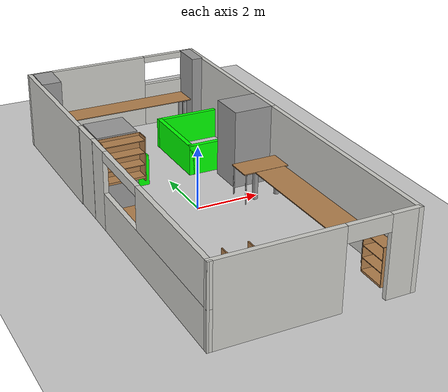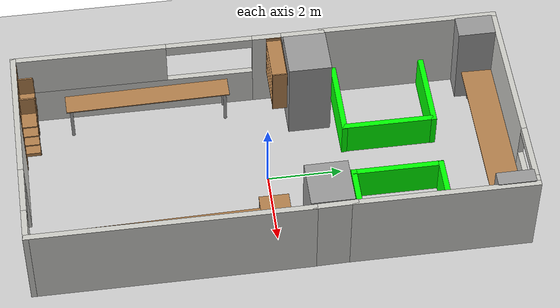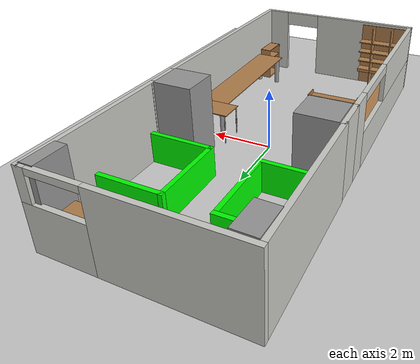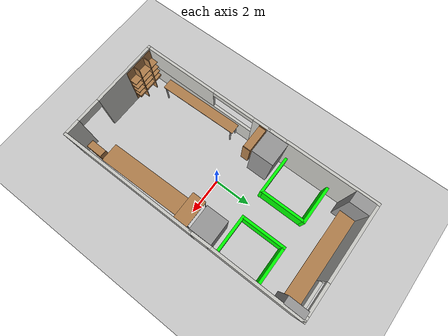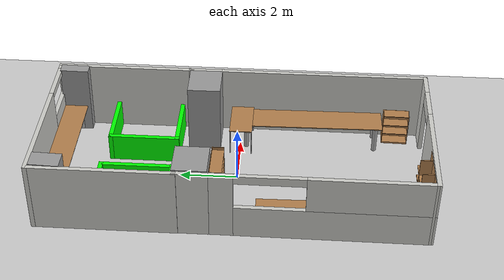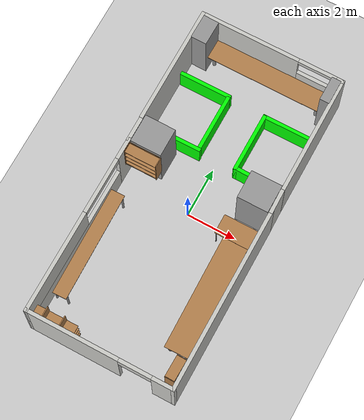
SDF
<sdf version="1.7">
 <world name="default">
  <light name="sun" type="directional">
   <pose>0 0 10 0 -0 0</pose>
   <diffuse>0.8 0.8 0.8 1</diffuse>
   <specular>0.2 0.2 0.2 1</specular>
   <attenuation>
    <range>1000</range>
    <constant>0.9</constant>
    <linear>0.01</linear>
    <quadratic>0.001</quadratic>
   </attenuation>
   <direction>-0.5 0.1 -0.9</direction>
   <spot><inner_angle>0</inner_angle><outer_angle>0</outer_angle><falloff>0</falloff></spot>
  </light>
  <model name="ground_plane">
   <static>1</static>
   <link name="link">
    <collision name="collision">
     <geometry><plane><normal>0 0 1</normal><size>100 100</size></plane></geometry>
     <surface>
      <contact><collide_bitmask>65535</collide_bitmask></contact>
      <friction><ode><mu>100</mu><mu2>50</mu2></ode></friction>
     </surface>
    </collision>
    <visual name="visual">
     <cast_shadows>0</cast_shadows>
     <geometry><plane><normal>0 0 1</normal><size>100 100</size></plane></geometry>
     <material>
      <script><uri>file://media/materials/scripts/gazebo.material</uri><name>Gazebo/Grey</name></script>
     </material>
    </visual>
   </link>
  </model>
  <gravity>0 0 -9.8</gravity>
  <magnetic_field>6e-06 2.3e-05 -4.2e-05</magnetic_field>
  <atmosphere type="adiabatic"/>
  <physics type="ode">
   <max_step_size>0.001</max_step_size>
   <real_time_factor>1</real_time_factor>
   <real_time_update_rate>1000</real_time_update_rate>
  </physics>
  <scene><ambient>0.4 0.4 0.4 1</ambient><background>0.7 0.7 0.7 1</background><shadows>1</shadows></scene>
  <audio><device>default</device></audio>
  <spherical_coordinates>
   <surface_model>EARTH_WGS84</surface_model>
   <latitude_deg>0</latitude_deg>
   <longitude_deg>0</longitude_deg>
   <elevation>0</elevation>
   <heading_deg>0</heading_deg>
  </spherical_coordinates>
  <model name="bookshelf_0">
   <static>1</static>
   <link name="link">
    <inertial><mass>1</mass></inertial>
    <collision name="back">
     <pose>0 0.005 0.6 0 -0 0</pose>
     <geometry><box><size>0.9 0.01 1.2</size></box></geometry>
    </collision>
    <visual name="visual1">
     <pose>0 0.005 0.6 0 -0 0</pose>
     <geometry><box><size>0.9 0.01 1.2</size></box></geometry>
     <material>
      <script><uri>file://media/materials/scripts/gazebo.material</uri><name>Gazebo/Wood</name></script>
     </material>
    </visual>
    <collision name="left_side">
     <pose>0.45 -0.195 0.6 0 -0 0</pose>
     <geometry><box><size>0.02 0.4 1.2</size></box></geometry>
    </collision>
    <visual name="visual2">
     <pose>0.45 -0.195 0.6 0 -0 0</pose>
     <geometry><box><size>0.02 0.4 1.2</size></box></geometry>
     <material>
      <script><uri>file://media/materials/scripts/gazebo.material</uri><name>Gazebo/Wood</name></script>
     </material>
    </visual>
    <collision name="right_side">
     <pose>-0.45 -0.195 0.6 0 -0 0</pose>
     <geometry><box><size>0.02 0.4 1.2</size></box></geometry>
    </collision>
    <visual name="visual3">
     <pose>-0.45 -0.195 0.6 0 -0 0</pose>
     <geometry><box><size>0.02 0.4 1.2</size></box></geometry>
     <material>
      <script><uri>file://media/materials/scripts/gazebo.material</uri><name>Gazebo/Wood</name></script>
     </material>
    </visual>
    <collision name="bottom">
     <pose>0 -0.195 0.03 0 -0 0</pose>
     <geometry><box><size>0.88 0.4 0.06</size></box></geometry>
    </collision>
    <visual name="visual4">
     <pose>0 -0.195 0.03 0 -0 0</pose>
     <geometry><box><size>0.88 0.4 0.06</size></box></geometry>
     <material>
      <script><uri>file://media/materials/scripts/gazebo.material</uri><name>Gazebo/Wood</name></script>
     </material>
    </visual>
    <collision name="top">
     <pose>0 -0.195 1.19 0 -0 0</pose>
     <geometry><box><size>0.88 0.4 0.02</size></box></geometry>
    </collision>
    <visual name="visual5">
     <pose>0 -0.195 1.19 0 -0 0</pose>
     <geometry><box><size>0.88 0.4 0.02</size></box></geometry>
     <material>
      <script><uri>file://media/materials/scripts/gazebo.material</uri><name>Gazebo/Wood</name></script>
     </material>
    </visual>
    <collision name="low_shelf">
     <pose>0 -0.195 0.43 0 -0 0</pose>
     <geometry><box><size>0.88 0.4 0.02</size></box></geometry>
    </collision>
    <visual name="visual6">
     <pose>0 -0.195 0.43 0 -0 0</pose>
     <geometry><box><size>0.88 0.4 0.02</size></box></geometry>
     <material>
      <script><uri>file://media/materials/scripts/gazebo.material</uri><name>Gazebo/Wood</name></script>
     </material>
    </visual>
    <collision name="high_shelf">
     <pose>0 -0.195 0.8 0 -0 0</pose>
     <geometry><box><size>0.88 0.4 0.02</size></box></geometry>
    </collision>
    <visual name="visual7">
     <pose>0 -0.195 0.8 0 -0 0</pose>
     <geometry><box><size>0.88 0.4 0.02</size></box></geometry>
     <material>
      <script><uri>file://media/materials/scripts/gazebo.material</uri><name>Gazebo/Wood</name></script>
     </material>
    </visual>
   </link>
   <pose>2.73004 -5.57226 0.00418 0 0 -1.59131</pose>
  </model>
  <model name="bookshelf">
   <link name="link">
    <inertial>
     <mass>1.65901</mass>
     <inertia>
      <ixx>0.0221916</ixx>
      <ixy>0</ixy>
      <ixz>0</ixz>
      <iyy>0.221936</iyy>
      <iyz>0</iyz>
      <izz>0.243984</izz>
     </inertia>
    </inertial>
    <pose>1.00602 -2.85901 1.20565 0 -0 0</pose>
    <visual name="visual6">
     <pose>0 -0.195 0.43 0 -0 0</pose>
     <geometry><box><size>1.2668 0.4 0.022734</size></box></geometry>
     <material>
      <script><uri>file://media/materials/scripts/gazebo.material</uri><name>Gazebo/Wood</name></script>
      <shader type="pixel"><normal_map>__default__</normal_map></shader>
      <ambient>1 1 1 1</ambient>
      <diffuse>1 1 1 1</diffuse>
      <specular>0.2 0.2 0.2 1</specular>
      <emissive>0 0 0 1</emissive>
     </material>
    </visual>
    <visual name="visual4">
     <pose>0 -0.195 0.03 0 -0 0</pose>
     <geometry><box><size>1.2668 0.4 0.06864</size></box></geometry>
     <material>
      <script><uri>file://media/materials/scripts/gazebo.material</uri><name>Gazebo/Wood</name></script>
      <shader type="pixel"><normal_map>__default__</normal_map></shader>
      <ambient>1 1 1 1</ambient>
      <diffuse>1 1 1 1</diffuse>
      <specular>0.2 0.2 0.2 1</specular>
      <emissive>0 0 0 1</emissive>
     </material>
    </visual>
    <visual name="visual2">
     <pose>0.65 -0.195 0.6 0 -0 0</pose>
     <geometry><box><size>0.029502 0.4 1.38625</size></box></geometry>
     <material>
      <script><uri>file://media/materials/scripts/gazebo.material</uri><name>Gazebo/Wood</name></script>
      <shader type="pixel"><normal_map>__default__</normal_map></shader>
      <ambient>1 1 1 1</ambient>
      <diffuse>1 1 1 1</diffuse>
      <specular>0.2 0.2 0.2 1</specular>
      <emissive>0 0 0 1</emissive>
     </material>
    </visual>
    <visual name="visual1">
     <pose>0 0.005 0.6 0 -0 0</pose>
     <geometry><box><size>1.29559 0.01 1.38625</size></box></geometry>
     <material>
      <script><uri>file://media/materials/scripts/gazebo.material</uri><name>Gazebo/Wood</name></script>
      <shader type="pixel"><normal_map>__default__</normal_map></shader>
      <ambient>1 1 1 1</ambient>
      <diffuse>1 1 1 1</diffuse>
      <specular>0.2 0.2 0.2 1</specular>
      <emissive>0 0 0 1</emissive>
     </material>
    </visual>
    <visual name="visual5">
     <pose>0 -0.195 1.19 0 -0 0</pose>
     <geometry><box><size>1.2668 0.4 0.022734</size></box></geometry>
     <material>
      <script><uri>file://media/materials/scripts/gazebo.material</uri><name>Gazebo/Wood</name></script>
      <shader type="pixel"><normal_map>__default__</normal_map></shader>
      <ambient>1 1 1 1</ambient>
      <diffuse>1 1 1 1</diffuse>
      <specular>0.2 0.2 0.2 1</specular>
      <emissive>0 0 0 1</emissive>
     </material>
    </visual>
    <visual name="visual7">
     <pose>0 -0.195 0.8 0 -0 0</pose>
     <geometry><box><size>1.2668 0.4 0.022734</size></box></geometry>
     <material>
      <script><uri>file://media/materials/scripts/gazebo.material</uri><name>Gazebo/Wood</name></script>
      <shader type="pixel"><normal_map>__default__</normal_map></shader>
      <ambient>1 1 1 1</ambient>
      <diffuse>1 1 1 1</diffuse>
      <specular>0.2 0.2 0.2 1</specular>
      <emissive>0 0 0 1</emissive>
     </material>
    </visual>
    <visual name="visual3">
     <pose>-0.65 -0.195 0.6 0 -0 0</pose>
     <geometry><box><size>0.029502 0.4 1.38625</size></box></geometry>
     <material>
      <script><uri>file://media/materials/scripts/gazebo.material</uri><name>Gazebo/Wood</name></script>
      <shader type="pixel"><normal_map>__default__</normal_map></shader>
      <ambient>1 1 1 1</ambient>
      <diffuse>1 1 1 1</diffuse>
      <specular>0.2 0.2 0.2 1</specular>
      <emissive>0 0 0 1</emissive>
     </material>
    </visual>
    <collision name="back">
     <pose>0 0.005 0.6 0 -0 0</pose>
     <geometry><box><size>1.29559 0.01 1.38625</size></box></geometry>
     <surface>
      <friction>
       <ode><mu>1</mu><mu2>1</mu2><fdir1>0 0 0</fdir1><slip1>0</slip1><slip2>0</slip2></ode>
       <torsional>
        <coefficient>1</coefficient>
        <patch_radius>0</patch_radius>
        <surface_radius>0</surface_radius>
        <use_patch_radius>1</use_patch_radius>
        <ode><slip>0</slip></ode>
       </torsional>
      </friction>
      <bounce><restitution_coefficient>0</restitution_coefficient><threshold>1e+06</threshold></bounce>
      <contact>
       <collide_without_contact>0</collide_without_contact>
       <collide_without_contact_bitmask>1</collide_without_contact_bitmask>
       <collide_bitmask>1</collide_bitmask>
       <ode>
        <soft_cfm>0</soft_cfm>
        <soft_erp>0.2</soft_erp>
        <kp>1e+13</kp>
        <kd>1</kd>
        <max_vel>0.01</max_vel>
        <min_depth>0</min_depth>
       </ode>
       <bullet>
        <split_impulse>1</split_impulse>
        <split_impulse_penetration_threshold>-0.01</split_impulse_penetration_threshold>
        <soft_cfm>0</soft_cfm>
        <soft_erp>0.2</soft_erp>
        <kp>1e+13</kp>
        <kd>1</kd>
       </bullet>
      </contact>
     </surface>
    </collision>
    <collision name="left_side">
     <pose>0.45 -0.195 0.6 0 -0 0</pose>
     <geometry><box><size>0.029502 0.4 1.38625</size></box></geometry>
     <surface>
      <friction>
       <ode><mu>1</mu><mu2>1</mu2><fdir1>0 0 0</fdir1><slip1>0</slip1><slip2>0</slip2></ode>
       <torsional>
        <coefficient>1</coefficient>
        <patch_radius>0</patch_radius>
        <surface_radius>0</surface_radius>
        <use_patch_radius>1</use_patch_radius>
        <ode><slip>0</slip></ode>
       </torsional>
      </friction>
      <bounce><restitution_coefficient>0</restitution_coefficient><threshold>1e+06</threshold></bounce>
      <contact>
       <collide_without_contact>0</collide_without_contact>
       <collide_without_contact_bitmask>1</collide_without_contact_bitmask>
       <collide_bitmask>1</collide_bitmask>
       <ode>
        <soft_cfm>0</soft_cfm>
        <soft_erp>0.2</soft_erp>
        <kp>1e+13</kp>
        <kd>1</kd>
        <max_vel>0.01</max_vel>
        <min_depth>0</min_depth>
       </ode>
       <bullet>
        <split_impulse>1</split_impulse>
        <split_impulse_penetration_threshold>-0.01</split_impulse_penetration_threshold>
        <soft_cfm>0</soft_cfm>
        <soft_erp>0.2</soft_erp>
        <kp>1e+13</kp>
        <kd>1</kd>
       </bullet>
      </contact>
     </surface>
    </collision>
    <collision name="bottom">
     <pose>0 -0.195 0.03 0 -0 0</pose>
     <geometry><box><size>1.2668 0.4 0.06864</size></box></geometry>
     <surface>
      <friction>
       <ode><mu>1</mu><mu2>1</mu2><fdir1>0 0 0</fdir1><slip1>0</slip1><slip2>0</slip2></ode>
       <torsional>
        <coefficient>1</coefficient>
        <patch_radius>0</patch_radius>
        <surface_radius>0</surface_radius>
        <use_patch_radius>1</use_patch_radius>
        <ode><slip>0</slip></ode>
       </torsional>
      </friction>
      <bounce><restitution_coefficient>0</restitution_coefficient><threshold>1e+06</threshold></bounce>
      <contact>
       <collide_without_contact>0</collide_without_contact>
       <collide_without_contact_bitmask>1</collide_without_contact_bitmask>
       <collide_bitmask>1</collide_bitmask>
       <ode>
        <soft_cfm>0</soft_cfm>
        <soft_erp>0.2</soft_erp>
        <kp>1e+13</kp>
        <kd>1</kd>
        <max_vel>0.01</max_vel>
        <min_depth>0</min_depth>
       </ode>
       <bullet>
        <split_impulse>1</split_impulse>
        <split_impulse_penetration_threshold>-0.01</split_impulse_penetration_threshold>
        <soft_cfm>0</soft_cfm>
        <soft_erp>0.2</soft_erp>
        <kp>1e+13</kp>
        <kd>1</kd>
       </bullet>
      </contact>
     </surface>
    </collision>
    <collision name="right_side">
     <pose>-0.45 -0.195 0.6 0 -0 0</pose>
     <geometry><box><size>0.029502 0.4 1.38625</size></box></geometry>
     <surface>
      <friction>
       <ode><mu>1</mu><mu2>1</mu2><fdir1>0 0 0</fdir1><slip1>0</slip1><slip2>0</slip2></ode>
       <torsional>
        <coefficient>1</coefficient>
        <patch_radius>0</patch_radius>
        <surface_radius>0</surface_radius>
        <use_patch_radius>1</use_patch_radius>
        <ode><slip>0</slip></ode>
       </torsional>
      </friction>
      <bounce><restitution_coefficient>0</restitution_coefficient><threshold>1e+06</threshold></bounce>
      <contact>
       <collide_without_contact>0</collide_without_contact>
       <collide_without_contact_bitmask>1</collide_without_contact_bitmask>
       <collide_bitmask>1</collide_bitmask>
       <ode>
        <soft_cfm>0</soft_cfm>
        <soft_erp>0.2</soft_erp>
        <kp>1e+13</kp>
        <kd>1</kd>
        <max_vel>0.01</max_vel>
        <min_depth>0</min_depth>
       </ode>
       <bullet>
        <split_impulse>1</split_impulse>
        <split_impulse_penetration_threshold>-0.01</split_impulse_penetration_threshold>
        <soft_cfm>0</soft_cfm>
        <soft_erp>0.2</soft_erp>
        <kp>1e+13</kp>
        <kd>1</kd>
       </bullet>
      </contact>
     </surface>
    </collision>
    <collision name="top">
     <pose>0 -0.195 1.19 0 -0 0</pose>
     <geometry><box><size>1.2668 0.4 0.022734</size></box></geometry>
     <surface>
      <friction>
       <ode><mu>1</mu><mu2>1</mu2><fdir1>0 0 0</fdir1><slip1>0</slip1><slip2>0</slip2></ode>
       <torsional>
        <coefficient>1</coefficient>
        <patch_radius>0</patch_radius>
        <surface_radius>0</surface_radius>
        <use_patch_radius>1</use_patch_radius>
        <ode><slip>0</slip></ode>
       </torsional>
      </friction>
      <bounce><restitution_coefficient>0</restitution_coefficient><threshold>1e+06</threshold></bounce>
      <contact>
       <collide_without_contact>0</collide_without_contact>
       <collide_without_contact_bitmask>1</collide_without_contact_bitmask>
       <collide_bitmask>1</collide_bitmask>
       <ode>
        <soft_cfm>0</soft_cfm>
        <soft_erp>0.2</soft_erp>
        <kp>1e+13</kp>
        <kd>1</kd>
        <max_vel>0.01</max_vel>
        <min_depth>0</min_depth>
       </ode>
       <bullet>
        <split_impulse>1</split_impulse>
        <split_impulse_penetration_threshold>-0.01</split_impulse_penetration_threshold>
        <soft_cfm>0</soft_cfm>
        <soft_erp>0.2</soft_erp>
        <kp>1e+13</kp>
        <kd>1</kd>
       </bullet>
      </contact>
     </surface>
    </collision>
    <collision name="high_shelf">
     <pose>0 -0.195 0.8 0 -0 0</pose>
     <geometry><box><size>1.2668 0.4 0.022734</size></box></geometry>
     <surface>
      <friction>
       <ode><mu>1</mu><mu2>1</mu2><fdir1>0 0 0</fdir1><slip1>0</slip1><slip2>0</slip2></ode>
       <torsional>
        <coefficient>1</coefficient>
        <patch_radius>0</patch_radius>
        <surface_radius>0</surface_radius>
        <use_patch_radius>1</use_patch_radius>
        <ode><slip>0</slip></ode>
       </torsional>
      </friction>
      <bounce><restitution_coefficient>0</restitution_coefficient><threshold>1e+06</threshold></bounce>
      <contact>
       <collide_without_contact>0</collide_without_contact>
       <collide_without_contact_bitmask>1</collide_without_contact_bitmask>
       <collide_bitmask>1</collide_bitmask>
       <ode>
        <soft_cfm>0</soft_cfm>
        <soft_erp>0.2</soft_erp>
        <kp>1e+13</kp>
        <kd>1</kd>
        <max_vel>0.01</max_vel>
        <min_depth>0</min_depth>
       </ode>
       <bullet>
        <split_impulse>1</split_impulse>
        <split_impulse_penetration_threshold>-0.01</split_impulse_penetration_threshold>
        <soft_cfm>0</soft_cfm>
        <soft_erp>0.2</soft_erp>
        <kp>1e+13</kp>
        <kd>1</kd>
       </bullet>
      </contact>
     </surface>
    </collision>
    <collision name="low_shelf">
     <pose>0 -0.195 0.43 0 -0 0</pose>
     <geometry><box><size>1.2668 0.4 0.022734</size></box></geometry>
     <surface>
      <friction>
       <ode><mu>1</mu><mu2>1</mu2><fdir1>0 0 0</fdir1><slip1>0</slip1><slip2>0</slip2></ode>
       <torsional>
        <coefficient>1</coefficient>
        <patch_radius>0</patch_radius>
        <surface_radius>0</surface_radius>
        <use_patch_radius>1</use_patch_radius>
        <ode><slip>0</slip></ode>
       </torsional>
      </friction>
      <bounce><restitution_coefficient>0</restitution_coefficient><threshold>1e+06</threshold></bounce>
      <contact>
       <collide_without_contact>0</collide_without_contact>
       <collide_without_contact_bitmask>1</collide_without_contact_bitmask>
       <collide_bitmask>1</collide_bitmask>
       <ode>
        <soft_cfm>0</soft_cfm>
        <soft_erp>0.2</soft_erp>
        <kp>1e+13</kp>
        <kd>1</kd>
        <max_vel>0.01</max_vel>
        <min_depth>0</min_depth>
       </ode>
       <bullet>
        <split_impulse>1</split_impulse>
        <split_impulse_penetration_threshold>-0.01</split_impulse_penetration_threshold>
        <soft_cfm>0</soft_cfm>
        <soft_erp>0.2</soft_erp>
        <kp>1e+13</kp>
        <kd>1</kd>
       </bullet>
      </contact>
     </surface>
    </collision>
   </link>
   <static>1</static>
   <pose>-3.16974 3.57257 0 0 -0 0</pose>
  </model>
  <model name="labview1">
   <link name="Wall_0">
    <pose>-0.008541 6.52312 0 0 -0 0</pose>
    <visual name="Wall_0_Visual_0">
     <pose>-0.939832 0 1.25 0 -0 0</pose>
     <geometry><box><size>4.12034 0.15 2.5</size></box></geometry>
     <material>
      <script><uri>file://media/materials/scripts/gazebo.material</uri><name>Gazebo/CeilingTiled</name></script>
      <ambient>1 1 1 1</ambient>
      <shader type="pixel"/>
     </material>
     <meta><layer>0</layer></meta>
    </visual>
    <visual name="Wall_0_Visual_1">
     <pose>2.06017 0 0.75 0 -0 0</pose>
     <geometry><box><size>1.87966 0.15 1.5</size></box></geometry>
     <material>
      <script><uri>file://media/materials/scripts/gazebo.material</uri><name>Gazebo/CeilingTiled</name></script>
      <ambient>1 1 1 1</ambient>
      <shader type="pixel"/>
     </material>
     <meta><layer>0</layer></meta>
    </visual>
    <visual name="Wall_0_Visual_3">
     <pose>1.89841 0 2.4 0 -0 0</pose>
     <geometry><box><size>1.55614 0.15 0.2</size></box></geometry>
     <material>
      <script><uri>file://media/materials/scripts/gazebo.material</uri><name>Gazebo/CeilingTiled</name></script>
      <ambient>1 1 1 1</ambient>
      <shader type="pixel"/>
     </material>
     <meta><layer>0</layer></meta>
    </visual>
    <visual name="Wall_0_Visual_2">
     <pose>2.83824 0 2 0 -0 0</pose>
     <geometry><box><size>0.32352 0.15 1</size></box></geometry>
     <material>
      <script><uri>file://media/materials/scripts/gazebo.material</uri><name>Gazebo/CeilingTiled</name></script>
      <ambient>1 1 1 1</ambient>
      <shader type="pixel"/>
     </material>
     <meta><layer>0</layer></meta>
    </visual>
    <collision name="Wall_0_Collision_0">
     <pose>-0.939832 0 1.25 0 -0 0</pose>
     <geometry><box><size>4.12034 0.15 2.5</size></box></geometry>
     <surface>
      <friction>
       <ode><mu>1</mu><mu2>1</mu2><fdir1>0 0 0</fdir1><slip1>0</slip1><slip2>0</slip2></ode>
       <torsional>
        <coefficient>1</coefficient>
        <patch_radius>0</patch_radius>
        <surface_radius>0</surface_radius>
        <use_patch_radius>1</use_patch_radius>
        <ode><slip>0</slip></ode>
       </torsional>
      </friction>
      <bounce><restitution_coefficient>0</restitution_coefficient><threshold>1e+06</threshold></bounce>
      <contact>
       <collide_without_contact>0</collide_without_contact>
       <collide_without_contact_bitmask>1</collide_without_contact_bitmask>
       <collide_bitmask>1</collide_bitmask>
       <ode>
        <soft_cfm>0</soft_cfm>
        <soft_erp>0.2</soft_erp>
        <kp>1e+13</kp>
        <kd>1</kd>
        <max_vel>0.01</max_vel>
        <min_depth>0</min_depth>
       </ode>
       <bullet>
        <split_impulse>1</split_impulse>
        <split_impulse_penetration_threshold>-0.01</split_impulse_penetration_threshold>
        <soft_cfm>0</soft_cfm>
        <soft_erp>0.2</soft_erp>
        <kp>1e+13</kp>
        <kd>1</kd>
       </bullet>
      </contact>
     </surface>
    </collision>
    <collision name="Wall_0_Collision_1">
     <pose>2.06017 0 0.75 0 -0 0</pose>
     <geometry><box><size>1.87966 0.15 1.5</size></box></geometry>
     <surface>
      <friction>
       <ode><mu>1</mu><mu2>1</mu2><fdir1>0 0 0</fdir1><slip1>0</slip1><slip2>0</slip2></ode>
       <torsional>
        <coefficient>1</coefficient>
        <patch_radius>0</patch_radius>
        <surface_radius>0</surface_radius>
        <use_patch_radius>1</use_patch_radius>
        <ode><slip>0</slip></ode>
       </torsional>
      </friction>
      <bounce><restitution_coefficient>0</restitution_coefficient><threshold>1e+06</threshold></bounce>
      <contact>
       <collide_without_contact>0</collide_without_contact>
       <collide_without_contact_bitmask>1</collide_without_contact_bitmask>
       <collide_bitmask>1</collide_bitmask>
       <ode>
        <soft_cfm>0</soft_cfm>
        <soft_erp>0.2</soft_erp>
        <kp>1e+13</kp>
        <kd>1</kd>
        <max_vel>0.01</max_vel>
        <min_depth>0</min_depth>
       </ode>
       <bullet>
        <split_impulse>1</split_impulse>
        <split_impulse_penetration_threshold>-0.01</split_impulse_penetration_threshold>
        <soft_cfm>0</soft_cfm>
        <soft_erp>0.2</soft_erp>
        <kp>1e+13</kp>
        <kd>1</kd>
       </bullet>
      </contact>
     </surface>
    </collision>
    <collision name="Wall_0_Collision_2">
     <pose>2.83824 0 2 0 -0 0</pose>
     <geometry><box><size>0.32352 0.15 1</size></box></geometry>
     <surface>
      <friction>
       <ode><mu>1</mu><mu2>1</mu2><fdir1>0 0 0</fdir1><slip1>0</slip1><slip2>0</slip2></ode>
       <torsional>
        <coefficient>1</coefficient>
        <patch_radius>0</patch_radius>
        <surface_radius>0</surface_radius>
        <use_patch_radius>1</use_patch_radius>
        <ode><slip>0</slip></ode>
       </torsional>
      </friction>
      <bounce><restitution_coefficient>0</restitution_coefficient><threshold>1e+06</threshold></bounce>
      <contact>
       <collide_without_contact>0</collide_without_contact>
       <collide_without_contact_bitmask>1</collide_without_contact_bitmask>
       <collide_bitmask>1</collide_bitmask>
       <ode>
        <soft_cfm>0</soft_cfm>
        <soft_erp>0.2</soft_erp>
        <kp>1e+13</kp>
        <kd>1</kd>
        <max_vel>0.01</max_vel>
        <min_depth>0</min_depth>
       </ode>
       <bullet>
        <split_impulse>1</split_impulse>
        <split_impulse_penetration_threshold>-0.01</split_impulse_penetration_threshold>
        <soft_cfm>0</soft_cfm>
        <soft_erp>0.2</soft_erp>
        <kp>1e+13</kp>
        <kd>1</kd>
       </bullet>
      </contact>
     </surface>
    </collision>
    <collision name="Wall_0_Collision_3">
     <pose>1.89841 0 2.4 0 -0 0</pose>
     <geometry><box><size>1.55614 0.15 0.2</size></box></geometry>
     <surface>
      <friction>
       <ode><mu>1</mu><mu2>1</mu2><fdir1>0 0 0</fdir1><slip1>0</slip1><slip2>0</slip2></ode>
       <torsional>
        <coefficient>1</coefficient>
        <patch_radius>0</patch_radius>
        <surface_radius>0</surface_radius>
        <use_patch_radius>1</use_patch_radius>
        <ode><slip>0</slip></ode>
       </torsional>
      </friction>
      <bounce><restitution_coefficient>0</restitution_coefficient><threshold>1e+06</threshold></bounce>
      <contact>
       <collide_without_contact>0</collide_without_contact>
       <collide_without_contact_bitmask>1</collide_without_contact_bitmask>
       <collide_bitmask>1</collide_bitmask>
       <ode>
        <soft_cfm>0</soft_cfm>
        <soft_erp>0.2</soft_erp>
        <kp>1e+13</kp>
        <kd>1</kd>
        <max_vel>0.01</max_vel>
        <min_depth>0</min_depth>
       </ode>
       <bullet>
        <split_impulse>1</split_impulse>
        <split_impulse_penetration_threshold>-0.01</split_impulse_penetration_threshold>
        <soft_cfm>0</soft_cfm>
        <soft_erp>0.2</soft_erp>
        <kp>1e+13</kp>
        <kd>1</kd>
       </bullet>
      </contact>
     </surface>
    </collision>
   </link>
   <link name="Wall_11">
    <pose>2.91646 4.16012 0 0 0 -1.5708</pose>
    <visual name="Wall_11_Visual">
     <pose>0 0 1.25 0 -0 0</pose>
     <geometry><box><size>4.876 0.15 2.5</size></box></geometry>
     <material>
      <script><uri>file://media/materials/scripts/gazebo.material</uri><name>Gazebo/CeilingTiled</name></script>
      <ambient>1 1 1 1</ambient>
      <shader type="pixel"/>
     </material>
     <meta><layer>0</layer></meta>
    </visual>
    <collision name="Wall_11_Collision">
     <pose>0 0 1.25 0 -0 0</pose>
     <geometry><box><size>4.876 0.15 2.5</size></box></geometry>
     <surface>
      <friction>
       <ode><mu>1</mu><mu2>1</mu2><fdir1>0 0 0</fdir1><slip1>0</slip1><slip2>0</slip2></ode>
       <torsional>
        <coefficient>1</coefficient>
        <patch_radius>0</patch_radius>
        <surface_radius>0</surface_radius>
        <use_patch_radius>1</use_patch_radius>
        <ode><slip>0</slip></ode>
       </torsional>
      </friction>
      <bounce><restitution_coefficient>0</restitution_coefficient><threshold>1e+06</threshold></bounce>
      <contact>
       <collide_without_contact>0</collide_without_contact>
       <collide_without_contact_bitmask>1</collide_without_contact_bitmask>
       <collide_bitmask>1</collide_bitmask>
       <ode>
        <soft_cfm>0</soft_cfm>
        <soft_erp>0.2</soft_erp>
        <kp>1e+13</kp>
        <kd>1</kd>
        <max_vel>0.01</max_vel>
        <min_depth>0</min_depth>
       </ode>
       <bullet>
        <split_impulse>1</split_impulse>
        <split_impulse_penetration_threshold>-0.01</split_impulse_penetration_threshold>
        <soft_cfm>0</soft_cfm>
        <soft_erp>0.2</soft_erp>
        <kp>1e+13</kp>
        <kd>1</kd>
       </bullet>
      </contact>
     </surface>
    </collision>
   </link>
   <link name="Wall_15">
    <pose>2.92039 1.30529 0 0 0 -1.554</pose>
    <visual name="Wall_15_Visual">
     <pose>0 0 1.25 0 -0 0</pose>
     <geometry><box><size>1.179 0.15 2.5</size></box></geometry>
     <material>
      <script><uri>file://media/materials/scripts/gazebo.material</uri><name>Gazebo/CeilingTiled</name></script>
      <ambient>1 1 1 1</ambient>
      <shader type="pixel"/>
     </material>
     <meta><layer>0</layer></meta>
    </visual>
    <collision name="Wall_15_Collision">
     <pose>0 0 1.25 0 -0 0</pose>
     <geometry><box><size>1.179 0.15 2.5</size></box></geometry>
     <surface>
      <friction>
       <ode><mu>1</mu><mu2>1</mu2><fdir1>0 0 0</fdir1><slip1>0</slip1><slip2>0</slip2></ode>
       <torsional>
        <coefficient>1</coefficient>
        <patch_radius>0</patch_radius>
        <surface_radius>0</surface_radius>
        <use_patch_radius>1</use_patch_radius>
        <ode><slip>0</slip></ode>
       </torsional>
      </friction>
      <bounce><restitution_coefficient>0</restitution_coefficient><threshold>1e+06</threshold></bounce>
      <contact>
       <collide_without_contact>0</collide_without_contact>
       <collide_without_contact_bitmask>1</collide_without_contact_bitmask>
       <collide_bitmask>1</collide_bitmask>
       <ode>
        <soft_cfm>0</soft_cfm>
        <soft_erp>0.2</soft_erp>
        <kp>1e+13</kp>
        <kd>1</kd>
        <max_vel>0.01</max_vel>
        <min_depth>0</min_depth>
       </ode>
       <bullet>
        <split_impulse>1</split_impulse>
        <split_impulse_penetration_threshold>-0.01</split_impulse_penetration_threshold>
        <soft_cfm>0</soft_cfm>
        <soft_erp>0.2</soft_erp>
        <kp>1e+13</kp>
        <kd>1</kd>
       </bullet>
      </contact>
     </surface>
    </collision>
   </link>
   <link name="Wall_17">
    <pose>2.93374 -2.87723 0 0 0 -1.5708</pose>
    <visual name="Wall_17_Visual">
     <pose>0 0 1.25 0 -0 0</pose>
     <geometry><box><size>7.441 0.15 2.5</size></box></geometry>
     <material>
      <script><uri>file://media/materials/scripts/gazebo.material</uri><name>Gazebo/CeilingTiled</name></script>
      <ambient>1 1 1 1</ambient>
      <shader type="pixel"/>
     </material>
     <meta><layer>0</layer></meta>
    </visual>
    <collision name="Wall_17_Collision">
     <pose>0 0 1.25 0 -0 0</pose>
     <geometry><box><size>7.441 0.15 2.5</size></box></geometry>
     <surface>
      <friction>
       <ode><mu>1</mu><mu2>1</mu2><fdir1>0 0 0</fdir1><slip1>0</slip1><slip2>0</slip2></ode>
       <torsional>
        <coefficient>1</coefficient>
        <patch_radius>0</patch_radius>
        <surface_radius>0</surface_radius>
        <use_patch_radius>1</use_patch_radius>
        <ode><slip>0</slip></ode>
       </torsional>
      </friction>
      <bounce><restitution_coefficient>0</restitution_coefficient><threshold>1e+06</threshold></bounce>
      <contact>
       <collide_without_contact>0</collide_without_contact>
       <collide_without_contact_bitmask>1</collide_without_contact_bitmask>
       <collide_bitmask>1</collide_bitmask>
       <ode>
        <soft_cfm>0</soft_cfm>
        <soft_erp>0.2</soft_erp>
        <kp>1e+13</kp>
        <kd>1</kd>
        <max_vel>0.01</max_vel>
        <min_depth>0</min_depth>
       </ode>
       <bullet>
        <split_impulse>1</split_impulse>
        <split_impulse_penetration_threshold>-0.01</split_impulse_penetration_threshold>
        <soft_cfm>0</soft_cfm>
        <soft_erp>0.2</soft_erp>
        <kp>1e+13</kp>
        <kd>1</kd>
       </bullet>
      </contact>
     </surface>
    </collision>
   </link>
   <link name="Wall_19">
    <pose>0.000101 -6.5228 0 0 -0 2.5e-05</pose>
    <visual name="Wall_19_Visual_0">
     <pose>-1.12074 0 1.25 0 -0 0</pose>
     <geometry><box><size>3.77581 0.15 2.5</size></box></geometry>
     <material>
      <script><uri>file://media/materials/scripts/gazebo.material</uri><name>Gazebo/CeilingTiled</name></script>
      <ambient>1 1 1 1</ambient>
      <shader type="pixel"/>
     </material>
     <meta><layer>0</layer></meta>
    </visual>
    <visual name="Wall_19_Visual_1">
     <pose>2.5466 0 1.25 0 -0 0</pose>
     <geometry><box><size>0.924084 0.15 2.5</size></box></geometry>
     <material>
      <script><uri>file://media/materials/scripts/gazebo.material</uri><name>Gazebo/CeilingTiled</name></script>
      <ambient>1 1 1 1</ambient>
      <shader type="pixel"/>
     </material>
     <meta><layer>0</layer></meta>
    </visual>
    <visual name="Wall_19_Visual_2">
     <pose>1.42586 0 2.25 0 -0 0</pose>
     <geometry><box><size>1.31739 0.15 0.5</size></box></geometry>
     <material>
      <script><uri>file://media/materials/scripts/gazebo.material</uri><name>Gazebo/CeilingTiled</name></script>
      <ambient>1 1 1 1</ambient>
      <shader type="pixel"/>
     </material>
     <meta><layer>0</layer></meta>
    </visual>
    <collision name="Wall_19_Collision_0">
     <pose>-1.12074 0 1.25 0 -0 0</pose>
     <geometry><box><size>3.77581 0.15 2.5</size></box></geometry>
     <surface>
      <friction>
       <ode><mu>1</mu><mu2>1</mu2><fdir1>0 0 0</fdir1><slip1>0</slip1><slip2>0</slip2></ode>
       <torsional>
        <coefficient>1</coefficient>
        <patch_radius>0</patch_radius>
        <surface_radius>0</surface_radius>
        <use_patch_radius>1</use_patch_radius>
        <ode><slip>0</slip></ode>
       </torsional>
      </friction>
      <bounce><restitution_coefficient>0</restitution_coefficient><threshold>1e+06</threshold></bounce>
      <contact>
       <collide_without_contact>0</collide_without_contact>
       <collide_without_contact_bitmask>1</collide_without_contact_bitmask>
       <collide_bitmask>1</collide_bitmask>
       <ode>
        <soft_cfm>0</soft_cfm>
        <soft_erp>0.2</soft_erp>
        <kp>1e+13</kp>
        <kd>1</kd>
        <max_vel>0.01</max_vel>
        <min_depth>0</min_depth>
       </ode>
       <bullet>
        <split_impulse>1</split_impulse>
        <split_impulse_penetration_threshold>-0.01</split_impulse_penetration_threshold>
        <soft_cfm>0</soft_cfm>
        <soft_erp>0.2</soft_erp>
        <kp>1e+13</kp>
        <kd>1</kd>
       </bullet>
      </contact>
     </surface>
    </collision>
    <collision name="Wall_19_Collision_1">
     <pose>2.5466 0 1.25 0 -0 0</pose>
     <geometry><box><size>0.924084 0.15 2.5</size></box></geometry>
     <surface>
      <friction>
       <ode><mu>1</mu><mu2>1</mu2><fdir1>0 0 0</fdir1><slip1>0</slip1><slip2>0</slip2></ode>
       <torsional>
        <coefficient>1</coefficient>
        <patch_radius>0</patch_radius>
        <surface_radius>0</surface_radius>
        <use_patch_radius>1</use_patch_radius>
        <ode><slip>0</slip></ode>
       </torsional>
      </friction>
      <bounce><restitution_coefficient>0</restitution_coefficient><threshold>1e+06</threshold></bounce>
      <contact>
       <collide_without_contact>0</collide_without_contact>
       <collide_without_contact_bitmask>1</collide_without_contact_bitmask>
       <collide_bitmask>1</collide_bitmask>
       <ode>
        <soft_cfm>0</soft_cfm>
        <soft_erp>0.2</soft_erp>
        <kp>1e+13</kp>
        <kd>1</kd>
        <max_vel>0.01</max_vel>
        <min_depth>0</min_depth>
       </ode>
       <bullet>
        <split_impulse>1</split_impulse>
        <split_impulse_penetration_threshold>-0.01</split_impulse_penetration_threshold>
        <soft_cfm>0</soft_cfm>
        <soft_erp>0.2</soft_erp>
        <kp>1e+13</kp>
        <kd>1</kd>
       </bullet>
      </contact>
     </surface>
    </collision>
    <collision name="Wall_19_Collision_2">
     <pose>1.42586 0 2.25 0 -0 0</pose>
     <geometry><box><size>1.31739 0.15 0.5</size></box></geometry>
     <surface>
      <friction>
       <ode><mu>1</mu><mu2>1</mu2><fdir1>0 0 0</fdir1><slip1>0</slip1><slip2>0</slip2></ode>
       <torsional>
        <coefficient>1</coefficient>
        <patch_radius>0</patch_radius>
        <surface_radius>0</surface_radius>
        <use_patch_radius>1</use_patch_radius>
        <ode><slip>0</slip></ode>
       </torsional>
      </friction>
      <bounce><restitution_coefficient>0</restitution_coefficient><threshold>1e+06</threshold></bounce>
      <contact>
       <collide_without_contact>0</collide_without_contact>
       <collide_without_contact_bitmask>1</collide_without_contact_bitmask>
       <collide_bitmask>1</collide_bitmask>
       <ode>
        <soft_cfm>0</soft_cfm>
        <soft_erp>0.2</soft_erp>
        <kp>1e+13</kp>
        <kd>1</kd>
        <max_vel>0.01</max_vel>
        <min_depth>0</min_depth>
       </ode>
       <bullet>
        <split_impulse>1</split_impulse>
        <split_impulse_penetration_threshold>-0.01</split_impulse_penetration_threshold>
        <soft_cfm>0</soft_cfm>
        <soft_erp>0.2</soft_erp>
        <kp>1e+13</kp>
        <kd>1</kd>
       </bullet>
      </contact>
     </surface>
    </collision>
   </link>
   <link name="Wall_2">
    <pose>-2.93354 4.16012 0 0 0 -1.5708</pose>
    <visual name="Wall_2_Visual">
     <pose>0 0 1.25 0 -0 0</pose>
     <geometry><box><size>4.876 0.15 2.5</size></box></geometry>
     <material>
      <script><uri>file://media/materials/scripts/gazebo.material</uri><name>Gazebo/CeilingTiled</name></script>
      <ambient>1 1 1 1</ambient>
      <shader type="pixel"/>
     </material>
     <meta><layer>0</layer></meta>
    </visual>
    <collision name="Wall_2_Collision">
     <pose>0 0 1.25 0 -0 0</pose>
     <geometry><box><size>4.876 0.15 2.5</size></box></geometry>
     <surface>
      <friction>
       <ode><mu>1</mu><mu2>1</mu2><fdir1>0 0 0</fdir1><slip1>0</slip1><slip2>0</slip2></ode>
       <torsional>
        <coefficient>1</coefficient>
        <patch_radius>0</patch_radius>
        <surface_radius>0</surface_radius>
        <use_patch_radius>1</use_patch_radius>
        <ode><slip>0</slip></ode>
       </torsional>
      </friction>
      <bounce><restitution_coefficient>0</restitution_coefficient><threshold>1e+06</threshold></bounce>
      <contact>
       <collide_without_contact>0</collide_without_contact>
       <collide_without_contact_bitmask>1</collide_without_contact_bitmask>
       <collide_bitmask>1</collide_bitmask>
       <ode>
        <soft_cfm>0</soft_cfm>
        <soft_erp>0.2</soft_erp>
        <kp>1e+13</kp>
        <kd>1</kd>
        <max_vel>0.01</max_vel>
        <min_depth>0</min_depth>
       </ode>
       <bullet>
        <split_impulse>1</split_impulse>
        <split_impulse_penetration_threshold>-0.01</split_impulse_penetration_threshold>
        <soft_cfm>0</soft_cfm>
        <soft_erp>0.2</soft_erp>
        <kp>1e+13</kp>
        <kd>1</kd>
       </bullet>
      </contact>
     </surface>
    </collision>
   </link>
   <link name="Wall_5">
    <pose>-2.91836 1.28263 0 0 0 -1.5708</pose>
    <visual name="Wall_5_Visual">
     <pose>0 0 1.25 0 -0 0</pose>
     <geometry><box><size>1.17898 0.15 2.5</size></box></geometry>
     <material>
      <script><uri>file://media/materials/scripts/gazebo.material</uri><name>Gazebo/CeilingTiled</name></script>
      <ambient>1 1 1 1</ambient>
      <shader type="pixel"/>
     </material>
     <meta><layer>0</layer></meta>
    </visual>
    <collision name="Wall_5_Collision">
     <pose>0 0 1.25 0 -0 0</pose>
     <geometry><box><size>1.17898 0.15 2.5</size></box></geometry>
     <surface>
      <friction>
       <ode><mu>1</mu><mu2>1</mu2><fdir1>0 0 0</fdir1><slip1>0</slip1><slip2>0</slip2></ode>
       <torsional>
        <coefficient>1</coefficient>
        <patch_radius>0</patch_radius>
        <surface_radius>0</surface_radius>
        <use_patch_radius>1</use_patch_radius>
        <ode><slip>0</slip></ode>
       </torsional>
      </friction>
      <bounce><restitution_coefficient>0</restitution_coefficient><threshold>1e+06</threshold></bounce>
      <contact>
       <collide_without_contact>0</collide_without_contact>
       <collide_without_contact_bitmask>1</collide_without_contact_bitmask>
       <collide_bitmask>1</collide_bitmask>
       <ode>
        <soft_cfm>0</soft_cfm>
        <soft_erp>0.2</soft_erp>
        <kp>1e+13</kp>
        <kd>1</kd>
        <max_vel>0.01</max_vel>
        <min_depth>0</min_depth>
       </ode>
       <bullet>
        <split_impulse>1</split_impulse>
        <split_impulse_penetration_threshold>-0.01</split_impulse_penetration_threshold>
        <soft_cfm>0</soft_cfm>
        <soft_erp>0.2</soft_erp>
        <kp>1e+13</kp>
        <kd>1</kd>
       </bullet>
      </contact>
     </surface>
    </collision>
   </link>
   <link name="Wall_9">
    <pose>-2.9236 -2.87737 0 0 0 -1.57352</pose>
    <visual name="Wall_9_Visual_0">
     <pose>-3.25053 0 1.25 0 -0 0</pose>
     <geometry><box><size>0.940067 0.15 2.5</size></box></geometry>
     <material>
      <script><uri>file://media/materials/scripts/gazebo.material</uri><name>Gazebo/CeilingTiled</name></script>
      <ambient>1 1 1 1</ambient>
      <shader type="pixel"/>
     </material>
     <meta><layer>0</layer></meta>
    </visual>
    <visual name="Wall_9_Visual_1">
     <pose>0.470034 0 0.6 0 -0 0</pose>
     <geometry><box><size>6.50106 0.15 1.2</size></box></geometry>
     <material>
      <script><uri>file://media/materials/scripts/gazebo.material</uri><name>Gazebo/CeilingTiled</name></script>
      <ambient>1 1 1 1</ambient>
      <shader type="pixel"/>
     </material>
     <meta><layer>0</layer></meta>
    </visual>
    <visual name="Wall_9_Visual_2">
     <pose>1.63503 0 1.85 0 -0 0</pose>
     <geometry><box><size>4.17106 0.15 1.3</size></box></geometry>
     <material>
      <script><uri>file://media/materials/scripts/gazebo.material</uri><name>Gazebo/CeilingTiled</name></script>
      <ambient>1 1 1 1</ambient>
      <shader type="pixel"/>
     </material>
     <meta><layer>0</layer></meta>
    </visual>
    <visual name="Wall_9_Visual_3">
     <pose>-1.61549 0 2.35 0 -0 0</pose>
     <geometry><box><size>2.33 0.15 0.3</size></box></geometry>
     <material>
      <script><uri>file://media/materials/scripts/gazebo.material</uri><name>Gazebo/CeilingTiled</name></script>
      <ambient>1 1 1 1</ambient>
      <shader type="pixel"/>
     </material>
     <meta><layer>0</layer></meta>
    </visual>
    <collision name="Wall_9_Collision_0">
     <pose>-3.25053 0 1.25 0 -0 0</pose>
     <geometry><box><size>0.940067 0.15 2.5</size></box></geometry>
     <surface>
      <friction>
       <ode><mu>1</mu><mu2>1</mu2><fdir1>0 0 0</fdir1><slip1>0</slip1><slip2>0</slip2></ode>
       <torsional>
        <coefficient>1</coefficient>
        <patch_radius>0</patch_radius>
        <surface_radius>0</surface_radius>
        <use_patch_radius>1</use_patch_radius>
        <ode><slip>0</slip></ode>
       </torsional>
      </friction>
      <bounce><restitution_coefficient>0</restitution_coefficient><threshold>1e+06</threshold></bounce>
      <contact>
       <collide_without_contact>0</collide_without_contact>
       <collide_without_contact_bitmask>1</collide_without_contact_bitmask>
       <collide_bitmask>1</collide_bitmask>
       <ode>
        <soft_cfm>0</soft_cfm>
        <soft_erp>0.2</soft_erp>
        <kp>1e+13</kp>
        <kd>1</kd>
        <max_vel>0.01</max_vel>
        <min_depth>0</min_depth>
       </ode>
       <bullet>
        <split_impulse>1</split_impulse>
        <split_impulse_penetration_threshold>-0.01</split_impulse_penetration_threshold>
        <soft_cfm>0</soft_cfm>
        <soft_erp>0.2</soft_erp>
        <kp>1e+13</kp>
        <kd>1</kd>
       </bullet>
      </contact>
     </surface>
    </collision>
    <collision name="Wall_9_Collision_1">
     <pose>0.470034 0 0.6 0 -0 0</pose>
     <geometry><box><size>6.50106 0.15 1.2</size></box></geometry>
     <surface>
      <friction>
       <ode><mu>1</mu><mu2>1</mu2><fdir1>0 0 0</fdir1><slip1>0</slip1><slip2>0</slip2></ode>
       <torsional>
        <coefficient>1</coefficient>
        <patch_radius>0</patch_radius>
        <surface_radius>0</surface_radius>
        <use_patch_radius>1</use_patch_radius>
        <ode><slip>0</slip></ode>
       </torsional>
      </friction>
      <bounce><restitution_coefficient>0</restitution_coefficient><threshold>1e+06</threshold></bounce>
      <contact>
       <collide_without_contact>0</collide_without_contact>
       <collide_without_contact_bitmask>1</collide_without_contact_bitmask>
       <collide_bitmask>1</collide_bitmask>
       <ode>
        <soft_cfm>0</soft_cfm>
        <soft_erp>0.2</soft_erp>
        <kp>1e+13</kp>
        <kd>1</kd>
        <max_vel>0.01</max_vel>
        <min_depth>0</min_depth>
       </ode>
       <bullet>
        <split_impulse>1</split_impulse>
        <split_impulse_penetration_threshold>-0.01</split_impulse_penetration_threshold>
        <soft_cfm>0</soft_cfm>
        <soft_erp>0.2</soft_erp>
        <kp>1e+13</kp>
        <kd>1</kd>
       </bullet>
      </contact>
     </surface>
    </collision>
    <collision name="Wall_9_Collision_2">
     <pose>1.63503 0 1.85 0 -0 0</pose>
     <geometry><box><size>4.17106 0.15 1.3</size></box></geometry>
     <surface>
      <friction>
       <ode><mu>1</mu><mu2>1</mu2><fdir1>0 0 0</fdir1><slip1>0</slip1><slip2>0</slip2></ode>
       <torsional>
        <coefficient>1</coefficient>
        <patch_radius>0</patch_radius>
        <surface_radius>0</surface_radius>
        <use_patch_radius>1</use_patch_radius>
        <ode><slip>0</slip></ode>
       </torsional>
      </friction>
      <bounce><restitution_coefficient>0</restitution_coefficient><threshold>1e+06</threshold></bounce>
      <contact>
       <collide_without_contact>0</collide_without_contact>
       <collide_without_contact_bitmask>1</collide_without_contact_bitmask>
       <collide_bitmask>1</collide_bitmask>
       <ode>
        <soft_cfm>0</soft_cfm>
        <soft_erp>0.2</soft_erp>
        <kp>1e+13</kp>
        <kd>1</kd>
        <max_vel>0.01</max_vel>
        <min_depth>0</min_depth>
       </ode>
       <bullet>
        <split_impulse>1</split_impulse>
        <split_impulse_penetration_threshold>-0.01</split_impulse_penetration_threshold>
        <soft_cfm>0</soft_cfm>
        <soft_erp>0.2</soft_erp>
        <kp>1e+13</kp>
        <kd>1</kd>
       </bullet>
      </contact>
     </surface>
    </collision>
    <collision name="Wall_9_Collision_3">
     <pose>-1.61549 0 2.35 0 -0 0</pose>
     <geometry><box><size>2.33 0.15 0.3</size></box></geometry>
     <surface>
      <friction>
       <ode><mu>1</mu><mu2>1</mu2><fdir1>0 0 0</fdir1><slip1>0</slip1><slip2>0</slip2></ode>
       <torsional>
        <coefficient>1</coefficient>
        <patch_radius>0</patch_radius>
        <surface_radius>0</surface_radius>
        <use_patch_radius>1</use_patch_radius>
        <ode><slip>0</slip></ode>
       </torsional>
      </friction>
      <bounce><restitution_coefficient>0</restitution_coefficient><threshold>1e+06</threshold></bounce>
      <contact>
       <collide_without_contact>0</collide_without_contact>
       <collide_without_contact_bitmask>1</collide_without_contact_bitmask>
       <collide_bitmask>1</collide_bitmask>
       <ode>
        <soft_cfm>0</soft_cfm>
        <soft_erp>0.2</soft_erp>
        <kp>1e+13</kp>
        <kd>1</kd>
        <max_vel>0.01</max_vel>
        <min_depth>0</min_depth>
       </ode>
       <bullet>
        <split_impulse>1</split_impulse>
        <split_impulse_penetration_threshold>-0.01</split_impulse_penetration_threshold>
        <soft_cfm>0</soft_cfm>
        <soft_erp>0.2</soft_erp>
        <kp>1e+13</kp>
        <kd>1</kd>
       </bullet>
      </contact>
     </surface>
    </collision>
   </link>
   <static>1</static>
   <pose>0.021113 0.03546 0 0 -0 0</pose>
  </model>
  <model name="unit_box">
   <link name="link">
    <inertial>
     <mass>3.60494</mass>
     <inertia><ixx>2.3033</ixx><ixy>0</ixy><ixz>0</ixz><iyy>2.37592</iyy><iyz>0</iyz><izz>0.862411</izz></inertia>
    </inertial>
    <pose>0.115933 0.041317 0.781855 0 -0 0</pose>
    <visual name="visual">
     <geometry><box><size>1.2475 1.14652 2.52044</size></box></geometry>
     <material>
      <script><name>Gazebo/Grey</name><uri>file://media/materials/scripts/gazebo.material</uri></script>
      <shader type="pixel"/>
     </material>
    </visual>
    <collision name="collision">
     <geometry><box><size>1.2475 1.14652 2.52044</size></box></geometry>
     <surface>
      <friction>
       <ode><mu>1</mu><mu2>1</mu2><fdir1>0 0 0</fdir1><slip1>0</slip1><slip2>0</slip2></ode>
       <torsional>
        <coefficient>1</coefficient>
        <patch_radius>0</patch_radius>
        <surface_radius>0</surface_radius>
        <use_patch_radius>1</use_patch_radius>
        <ode><slip>0</slip></ode>
       </torsional>
      </friction>
      <bounce><restitution_coefficient>0</restitution_coefficient><threshold>1e+06</threshold></bounce>
      <contact>
       <collide_without_contact>0</collide_without_contact>
       <collide_without_contact_bitmask>1</collide_without_contact_bitmask>
       <collide_bitmask>1</collide_bitmask>
       <ode>
        <soft_cfm>0</soft_cfm>
        <soft_erp>0.2</soft_erp>
        <kp>1e+13</kp>
        <kd>1</kd>
        <max_vel>0.01</max_vel>
        <min_depth>0</min_depth>
       </ode>
       <bullet>
        <split_impulse>1</split_impulse>
        <split_impulse_penetration_threshold>-0.01</split_impulse_penetration_threshold>
        <soft_cfm>0</soft_cfm>
        <soft_erp>0.2</soft_erp>
        <kp>1e+13</kp>
        <kd>1</kd>
       </bullet>
      </contact>
     </surface>
    </collision>
   </link>
   <static>0</static>
   <pose>-2.29713 1.30804 0.478362 2e-06 -2e-06 -0.000169</pose>
  </model>
  <model name="unit_box_clone">
   <link name="link">
    <inertial>
     <mass>3.60494</mass>
     <inertia><ixx>2.3033</ixx><ixy>0</ixy><ixz>0</ixz><iyy>2.37592</iyy><iyz>0</iyz><izz>0.862411</izz></inertia>
    </inertial>
    <pose>0.115933 0.041317 0.781855 0 -0 0</pose>
    <visual name="visual">
     <geometry><box><size>1.2475 1.14652 2.52044</size></box></geometry>
     <material>
      <script><name>Gazebo/Grey</name><uri>file://media/materials/scripts/gazebo.material</uri></script>
      <shader type="pixel"/>
     </material>
    </visual>
    <collision name="collision">
     <geometry><box><size>1.2475 1.14652 2.52044</size></box></geometry>
     <surface>
      <friction>
       <ode><mu>1</mu><mu2>1</mu2><fdir1>0 0 0</fdir1><slip1>0</slip1><slip2>0</slip2></ode>
       <torsional>
        <coefficient>1</coefficient>
        <patch_radius>0</patch_radius>
        <surface_radius>0</surface_radius>
        <use_patch_radius>1</use_patch_radius>
        <ode><slip>0</slip></ode>
       </torsional>
      </friction>
      <bounce><restitution_coefficient>0</restitution_coefficient><threshold>1e+06</threshold></bounce>
      <contact>
       <collide_without_contact>0</collide_without_contact>
       <collide_without_contact_bitmask>1</collide_without_contact_bitmask>
       <collide_bitmask>1</collide_bitmask>
       <ode>
        <soft_cfm>0</soft_cfm>
        <soft_erp>0.2</soft_erp>
        <kp>1e+13</kp>
        <kd>1</kd>
        <max_vel>0.01</max_vel>
        <min_depth>0</min_depth>
       </ode>
       <bullet>
        <split_impulse>1</split_impulse>
        <split_impulse_penetration_threshold>-0.01</split_impulse_penetration_threshold>
        <soft_cfm>0</soft_cfm>
        <soft_erp>0.2</soft_erp>
        <kp>1e+13</kp>
        <kd>1</kd>
       </bullet>
      </contact>
     </surface>
    </collision>
   </link>
   <static>0</static>
   <pose>2.12011 1.2471 0.478365 0 -0 0.005847</pose>
  </model>
  <model name="space1">
   <pose>-1.41586 2.33273 0 0 -0 0</pose>
   <link name="Wall_0">
    <collision name="Wall_0_Collision">
     <geometry><box><size>2.15 0.15 1</size></box></geometry>
     <pose>0 0 0.5 0 -0 0</pose>
    </collision>
    <visual name="Wall_0_Visual">
     <pose>0 0 0.5 0 -0 0</pose>
     <geometry><box><size>2.15 0.15 1</size></box></geometry>
     <material>
      <script><uri>file://media/materials/scripts/gazebo.material</uri><name>Gazebo/Grey</name></script>
      <ambient>0 1 0 1</ambient>
     </material>
     <meta><layer>0</layer></meta>
    </visual>
    <pose>-0.320005 2.28621 0 0 -0 0</pose>
   </link>
   <link name="Wall_4">
    <collision name="Wall_4_Collision">
     <geometry><box><size>2.19563 0.15 1</size></box></geometry>
     <pose>0 0 0.5 0 -0 0</pose>
    </collision>
    <visual name="Wall_4_Visual">
     <pose>0 0 0.5 0 -0 0</pose>
     <geometry><box><size>2.19563 0.15 1</size></box></geometry>
     <material>
      <script><uri>file://media/materials/scripts/gazebo.material</uri><name>Gazebo/Grey</name></script>
      <ambient>0 1 0 1</ambient>
     </material>
     <meta><layer>0</layer></meta>
    </visual>
    <pose>-0.331973 -0.155252 0 0 -0 3.14159</pose>
   </link>
   <link name="Wall_6">
    <collision name="Wall_6_Collision">
     <geometry><box><size>2.5 0.15 1</size></box></geometry>
     <pose>0 0 0.5 0 -0 0</pose>
    </collision>
    <visual name="Wall_6_Visual">
     <pose>0 0 0.5 0 -0 0</pose>
     <geometry><box><size>2.5 0.15 1</size></box></geometry>
     <material>
      <script><uri>file://media/materials/scripts/gazebo.material</uri><name>Gazebo/Grey</name></script>
      <ambient>0 1 0 1</ambient>
     </material>
     <meta><layer>0</layer></meta>
    </visual>
    <pose>0.675631 1.01975 0 0 -0 1.5708</pose>
   </link>
   <static>1</static>
  </model>
  <model name="space2">
   <pose>1.46392 2.29956 0 0 -0 0</pose>
   <link name="Wall_10">
    <collision name="Wall_10_Collision">
     <geometry><box><size>2.5 0.15 1</size></box></geometry>
     <pose>0 0 0.5 0 -0 0</pose>
    </collision>
    <visual name="Wall_10_Visual">
     <pose>0 0 0.5 0 -0 0</pose>
     <geometry><box><size>2.5 0.15 1</size></box></geometry>
     <material>
      <script><uri>file://media/materials/scripts/gazebo.material</uri><name>Gazebo/Grey</name></script>
      <ambient>0 1 0 1</ambient>
     </material>
     <meta><layer>0</layer></meta>
    </visual>
    <pose>-0.633 1.063 0 0 -0 -1.5708</pose>
   </link>
   <link name="Wall_12">
    <collision name="Wall_12_Collision">
     <geometry><box><size>2.15 0.15 1</size></box></geometry>
     <pose>0 0 0.5 0 -0 0</pose>
    </collision>
    <visual name="Wall_12_Visual">
     <pose>0 0 0.5 0 -0 0</pose>
     <geometry><box><size>2.15 0.15 1</size></box></geometry>
     <material>
      <script><uri>file://media/materials/scripts/gazebo.material</uri><name>Gazebo/Grey</name></script>
      <ambient>0 1 0 1</ambient>
     </material>
     <meta><layer>0</layer></meta>
    </visual>
    <pose>0.367 -0.112 0 0 -0 0</pose>
   </link>
   <link name="Wall_8">
    <collision name="Wall_8_Collision">
     <geometry><box><size>2.15 0.15 1</size></box></geometry>
     <pose>0 0 0.5 0 -0 0</pose>
    </collision>
    <visual name="Wall_8_Visual">
     <pose>0 0 0.5 0 -0 0</pose>
     <geometry><box><size>2.15 0.15 1</size></box></geometry>
     <material>
      <script><uri>file://media/materials/scripts/gazebo.material</uri><name>Gazebo/Grey</name></script>
      <ambient>0 1 0 1</ambient>
     </material>
     <meta><layer>0</layer></meta>
    </visual>
    <pose>0.367 2.238 0 0 -0 0</pose>
   </link>
   <static>1</static>
  </model>
  <model name="unit_box_0">
   <link name="link">
    <inertial>
     <mass>1.64132</mass>
     <inertia>
      <ixx>1.04587</ixx>
      <ixy>0</ixy>
      <ixz>0</ixz>
      <iyy>0.964527</iyy>
      <iyz>0</iyz>
      <izz>0.192213</izz>
     </inertia>
    </inertial>
    <pose>-0.05747 0.263796 -0.017849 0 -0 0</pose>
    <visual name="visual">
     <geometry><box><size>0.636638 1 2.57809</size></box></geometry>
     <material>
      <script><name>Gazebo/Grey</name><uri>file://media/materials/scripts/gazebo.material</uri></script>
      <shader type="pixel"/>
     </material>
    </visual>
    <collision name="collision">
     <geometry><box><size>0.636638 1 2.57809</size></box></geometry>
     <surface>
      <friction>
       <ode><mu>1</mu><mu2>1</mu2><fdir1>0 0 0</fdir1><slip1>0</slip1><slip2>0</slip2></ode>
       <torsional>
        <coefficient>1</coefficient>
        <patch_radius>0</patch_radius>
        <surface_radius>0</surface_radius>
        <use_patch_radius>1</use_patch_radius>
        <ode><slip>0</slip></ode>
       </torsional>
      </friction>
      <bounce><restitution_coefficient>0</restitution_coefficient><threshold>1e+06</threshold></bounce>
      <contact>
       <collide_without_contact>0</collide_without_contact>
       <collide_without_contact_bitmask>1</collide_without_contact_bitmask>
       <collide_bitmask>1</collide_bitmask>
       <ode>
        <soft_cfm>0</soft_cfm>
        <soft_erp>0.2</soft_erp>
        <kp>1e+13</kp>
        <kd>1</kd>
        <max_vel>0.01</max_vel>
        <min_depth>0</min_depth>
       </ode>
       <bullet>
        <split_impulse>1</split_impulse>
        <split_impulse_penetration_threshold>-0.01</split_impulse_penetration_threshold>
        <soft_cfm>0</soft_cfm>
        <soft_erp>0.2</soft_erp>
        <kp>1e+13</kp>
        <kd>1</kd>
       </bullet>
      </contact>
     </surface>
    </collision>
   </link>
   <static>0</static>
   <pose>-2.47285 5.74765 1.25001 0.019924 -0.002649 -0.01577</pose>
  </model>
  <model name="unit_box_0_clone">
   <link name="link">
    <inertial>
     <mass>0.989344</mass>
     <inertia>
      <ixx>0.630422</ixx>
      <ixy>0</ixy>
      <ixz>0</ixz>
      <iyy>0.560118</iyy>
      <iyz>0</iyz>
      <izz>0.0945864</izz>
     </inertia>
    </inertial>
    <pose>-0.027265 0.256508 -0.017849 0 -0 0</pose>
    <visual name="visual">
     <geometry><box><size>0.383747 1 2.57809</size></box></geometry>
     <material>
      <script><name>Gazebo/Grey</name><uri>file://media/materials/scripts/gazebo.material</uri></script>
      <shader type="pixel"/>
     </material>
    </visual>
    <collision name="collision">
     <geometry><box><size>0.383747 1 2.57809</size></box></geometry>
     <surface>
      <friction>
       <ode><mu>1</mu><mu2>1</mu2><fdir1>0 0 0</fdir1><slip1>0</slip1><slip2>0</slip2></ode>
       <torsional>
        <coefficient>1</coefficient>
        <patch_radius>0</patch_radius>
        <surface_radius>0</surface_radius>
        <use_patch_radius>1</use_patch_radius>
        <ode><slip>0</slip></ode>
       </torsional>
      </friction>
      <bounce><restitution_coefficient>0</restitution_coefficient><threshold>1e+06</threshold></bounce>
      <contact>
       <collide_without_contact>0</collide_without_contact>
       <collide_without_contact_bitmask>1</collide_without_contact_bitmask>
       <collide_bitmask>1</collide_bitmask>
       <ode>
        <soft_cfm>0</soft_cfm>
        <soft_erp>0.2</soft_erp>
        <kp>1e+13</kp>
        <kd>1</kd>
        <max_vel>0.01</max_vel>
        <min_depth>0</min_depth>
       </ode>
       <bullet>
        <split_impulse>1</split_impulse>
        <split_impulse_penetration_threshold>-0.01</split_impulse_penetration_threshold>
        <soft_cfm>0</soft_cfm>
        <soft_erp>0.2</soft_erp>
        <kp>1e+13</kp>
        <kd>1</kd>
       </bullet>
      </contact>
     </surface>
    </collision>
   </link>
   <static>0</static>
   <pose>2.72806 5.785 1.24808 0.008866 -7.3e-05 -0.001573</pose>
  </model>
  <model name="table_0">
   <link name="link">
    <inertial>
     <inertia><ixx>0</ixx><ixy>0</ixy><ixz>0</ixz><iyy>0</iyy><iyz>0</iyz><izz>0</izz></inertia>
     <mass>0</mass>
    </inertial>
    <pose>1.16745 -0.333998 0 0 -0 0</pose>
    <visual name="front_left_leg">
     <pose>2.3 0.38 0.5 0 -0 0</pose>
     <geometry><cylinder><radius>0.0859649</radius><length>0.953962</length></cylinder></geometry>
     <material>
      <script><uri>file://media/materials/scripts/gazebo.material</uri><name>Gazebo/Grey</name></script>
      <shader type="pixel"><normal_map>__default__</normal_map></shader>
      <ambient>0.3 0.3 0.3 1</ambient>
      <diffuse>0.7 0.7 0.7 1</diffuse>
      <specular>0.01 0.01 0.01 1</specular>
      <emissive>0 0 0 1</emissive>
     </material>
    </visual>
    <visual name="back_left_leg">
     <pose>-2.3 0.38 0.5 0 -0 0</pose>
     <geometry><cylinder><radius>0.0859649</radius><length>0.953962</length></cylinder></geometry>
     <material>
      <script><uri>file://media/materials/scripts/gazebo.material</uri><name>Gazebo/Grey</name></script>
      <shader type="pixel"><normal_map>__default__</normal_map></shader>
      <ambient>0.3 0.3 0.3 1</ambient>
      <diffuse>0.7 0.7 0.7 1</diffuse>
      <specular>0.01 0.01 0.01 1</specular>
      <emissive>0 0 0 1</emissive>
     </material>
    </visual>
    <visual name="front_right_leg">
     <pose>2.3 -0.38 0.5 0 -0 0</pose>
     <geometry><cylinder><radius>0.0859649</radius><length>0.953962</length></cylinder></geometry>
     <material>
      <script><uri>file://media/materials/scripts/gazebo.material</uri><name>Gazebo/Grey</name></script>
      <shader type="pixel"><normal_map>__default__</normal_map></shader>
      <ambient>0.3 0.3 0.3 1</ambient>
      <diffuse>0.7 0.7 0.7 1</diffuse>
      <specular>0.01 0.01 0.01 1</specular>
      <emissive>0 0 0 1</emissive>
     </material>
    </visual>
    <visual name="visual1">
     <pose>0 0 1 0 -0 0</pose>
     <geometry><box><size>5.07081 1.01373 0.028898</size></box></geometry>
     <material>
      <script><uri>file://media/materials/scripts/gazebo.material</uri><name>Gazebo/Wood</name></script>
      <shader type="pixel"><normal_map>__default__</normal_map></shader>
      <ambient>1 1 1 1</ambient>
      <diffuse>1 1 1 1</diffuse>
      <specular>0.2 0.2 0.2 1</specular>
      <emissive>0 0 0 1</emissive>
     </material>
    </visual>
    <visual name="back_right_leg">
     <pose>-2.3 -0.38 0.5 0 -0 0</pose>
     <geometry><cylinder><radius>0.0859649</radius><length>0.953962</length></cylinder></geometry>
     <material>
      <script><uri>file://media/materials/scripts/gazebo.material</uri><name>Gazebo/Grey</name></script>
      <shader type="pixel"><normal_map>__default__</normal_map></shader>
      <ambient>0.3 0.3 0.3 1</ambient>
      <diffuse>0.7 0.7 0.7 1</diffuse>
      <specular>0.01 0.01 0.01 1</specular>
      <emissive>0 0 0 1</emissive>
     </material>
    </visual>
    <collision name="back_right_leg">
     <pose>-0.68 -0.38 0.5 0 -0 0</pose>
     <geometry><cylinder><radius>0.085966</radius><length>0.953962</length></cylinder></geometry>
     <surface>
      <friction>
       <ode><mu>1</mu><mu2>1</mu2><fdir1>0 0 0</fdir1><slip1>0</slip1><slip2>0</slip2></ode>
       <torsional>
        <coefficient>1</coefficient>
        <patch_radius>0</patch_radius>
        <surface_radius>0</surface_radius>
        <use_patch_radius>1</use_patch_radius>
        <ode><slip>0</slip></ode>
       </torsional>
      </friction>
      <bounce><restitution_coefficient>0</restitution_coefficient><threshold>1e+06</threshold></bounce>
      <contact>
       <collide_without_contact>0</collide_without_contact>
       <collide_without_contact_bitmask>1</collide_without_contact_bitmask>
       <collide_bitmask>1</collide_bitmask>
       <ode>
        <soft_cfm>0</soft_cfm>
        <soft_erp>0.2</soft_erp>
        <kp>1e+13</kp>
        <kd>1</kd>
        <max_vel>0.01</max_vel>
        <min_depth>0</min_depth>
       </ode>
       <bullet>
        <split_impulse>1</split_impulse>
        <split_impulse_penetration_threshold>-0.01</split_impulse_penetration_threshold>
        <soft_cfm>0</soft_cfm>
        <soft_erp>0.2</soft_erp>
        <kp>1e+13</kp>
        <kd>1</kd>
       </bullet>
      </contact>
     </surface>
    </collision>
    <collision name="front_right_leg">
     <pose>0.68 -0.38 0.5 0 -0 0</pose>
     <geometry><cylinder><radius>0.085966</radius><length>0.953962</length></cylinder></geometry>
     <surface>
      <friction>
       <ode><mu>1</mu><mu2>1</mu2><fdir1>0 0 0</fdir1><slip1>0</slip1><slip2>0</slip2></ode>
       <torsional>
        <coefficient>1</coefficient>
        <patch_radius>0</patch_radius>
        <surface_radius>0</surface_radius>
        <use_patch_radius>1</use_patch_radius>
        <ode><slip>0</slip></ode>
       </torsional>
      </friction>
      <bounce><restitution_coefficient>0</restitution_coefficient><threshold>1e+06</threshold></bounce>
      <contact>
       <collide_without_contact>0</collide_without_contact>
       <collide_without_contact_bitmask>1</collide_without_contact_bitmask>
       <collide_bitmask>1</collide_bitmask>
       <ode>
        <soft_cfm>0</soft_cfm>
        <soft_erp>0.2</soft_erp>
        <kp>1e+13</kp>
        <kd>1</kd>
        <max_vel>0.01</max_vel>
        <min_depth>0</min_depth>
       </ode>
       <bullet>
        <split_impulse>1</split_impulse>
        <split_impulse_penetration_threshold>-0.01</split_impulse_penetration_threshold>
        <soft_cfm>0</soft_cfm>
        <soft_erp>0.2</soft_erp>
        <kp>1e+13</kp>
        <kd>1</kd>
       </bullet>
      </contact>
     </surface>
    </collision>
    <collision name="back_left_leg">
     <pose>-0.68 0.38 0.5 0 -0 0</pose>
     <geometry><cylinder><radius>0.085966</radius><length>0.953962</length></cylinder></geometry>
     <surface>
      <friction>
       <ode><mu>1</mu><mu2>1</mu2><fdir1>0 0 0</fdir1><slip1>0</slip1><slip2>0</slip2></ode>
       <torsional>
        <coefficient>1</coefficient>
        <patch_radius>0</patch_radius>
        <surface_radius>0</surface_radius>
        <use_patch_radius>1</use_patch_radius>
        <ode><slip>0</slip></ode>
       </torsional>
      </friction>
      <bounce><restitution_coefficient>0</restitution_coefficient><threshold>1e+06</threshold></bounce>
      <contact>
       <collide_without_contact>0</collide_without_contact>
       <collide_without_contact_bitmask>1</collide_without_contact_bitmask>
       <collide_bitmask>1</collide_bitmask>
       <ode>
        <soft_cfm>0</soft_cfm>
        <soft_erp>0.2</soft_erp>
        <kp>1e+13</kp>
        <kd>1</kd>
        <max_vel>0.01</max_vel>
        <min_depth>0</min_depth>
       </ode>
       <bullet>
        <split_impulse>1</split_impulse>
        <split_impulse_penetration_threshold>-0.01</split_impulse_penetration_threshold>
        <soft_cfm>0</soft_cfm>
        <soft_erp>0.2</soft_erp>
        <kp>1e+13</kp>
        <kd>1</kd>
       </bullet>
      </contact>
     </surface>
    </collision>
    <collision name="surface">
     <pose>0 0 1 0 -0 0</pose>
     <geometry><box><size>5.07081 1.01373 0.028898</size></box></geometry>
     <surface>
      <friction>
       <ode><mu>0.6</mu><mu2>0.6</mu2><fdir1>0 0 0</fdir1><slip1>0</slip1><slip2>0</slip2></ode>
       <torsional>
        <coefficient>1</coefficient>
        <patch_radius>0</patch_radius>
        <surface_radius>0</surface_radius>
        <use_patch_radius>1</use_patch_radius>
        <ode><slip>0</slip></ode>
       </torsional>
      </friction>
      <bounce><restitution_coefficient>0</restitution_coefficient><threshold>1e+06</threshold></bounce>
      <contact>
       <collide_without_contact>0</collide_without_contact>
       <collide_without_contact_bitmask>1</collide_without_contact_bitmask>
       <collide_bitmask>1</collide_bitmask>
       <ode>
        <soft_cfm>0</soft_cfm>
        <soft_erp>0.2</soft_erp>
        <kp>1e+13</kp>
        <kd>1</kd>
        <max_vel>0.01</max_vel>
        <min_depth>0</min_depth>
       </ode>
       <bullet>
        <split_impulse>1</split_impulse>
        <split_impulse_penetration_threshold>-0.01</split_impulse_penetration_threshold>
        <soft_cfm>0</soft_cfm>
        <soft_erp>0.2</soft_erp>
        <kp>1e+13</kp>
        <kd>1</kd>
       </bullet>
      </contact>
     </surface>
    </collision>
    <collision name="front_left_leg">
     <pose>0.68 0.38 0.5 0 -0 0</pose>
     <geometry><cylinder><radius>0.085966</radius><length>0.953962</length></cylinder></geometry>
     <surface>
      <friction>
       <ode><mu>1</mu><mu2>1</mu2><fdir1>0 0 0</fdir1><slip1>0</slip1><slip2>0</slip2></ode>
       <torsional>
        <coefficient>1</coefficient>
        <patch_radius>0</patch_radius>
        <surface_radius>0</surface_radius>
        <use_patch_radius>1</use_patch_radius>
        <ode><slip>0</slip></ode>
       </torsional>
      </friction>
      <bounce><restitution_coefficient>0</restitution_coefficient><threshold>1e+06</threshold></bounce>
      <contact>
       <collide_without_contact>0</collide_without_contact>
       <collide_without_contact_bitmask>1</collide_without_contact_bitmask>
       <collide_bitmask>1</collide_bitmask>
       <ode>
        <soft_cfm>0</soft_cfm>
        <soft_erp>0.2</soft_erp>
        <kp>1e+13</kp>
        <kd>1</kd>
        <max_vel>0.01</max_vel>
        <min_depth>0</min_depth>
       </ode>
       <bullet>
        <split_impulse>1</split_impulse>
        <split_impulse_penetration_threshold>-0.01</split_impulse_penetration_threshold>
        <soft_cfm>0</soft_cfm>
        <soft_erp>0.2</soft_erp>
        <kp>1e+13</kp>
        <kd>1</kd>
       </bullet>
      </contact>
     </surface>
    </collision>
   </link>
   <static>1</static>
   <pose>2.56032 -1.33661 0 0 0 -1.55574</pose>
  </model>
  <model name="table">
   <static>1</static>
   <link name="link">
    <collision name="surface">
     <pose>0 0 1 0 -0 0</pose>
     <geometry><box><size>1.5 0.8 0.03</size></box></geometry>
     <surface><friction><ode><mu>0.6</mu><mu2>0.6</mu2></ode></friction></surface>
    </collision>
    <visual name="visual1">
     <pose>0 0 1 0 -0 0</pose>
     <geometry><box><size>1.5 0.8 0.03</size></box></geometry>
     <material>
      <script><uri>file://media/materials/scripts/gazebo.material</uri><name>Gazebo/Wood</name></script>
     </material>
    </visual>
    <collision name="front_left_leg">
     <pose>0.68 0.38 0.5 0 -0 0</pose>
     <geometry><cylinder><radius>0.02</radius><length>1</length></cylinder></geometry>
    </collision>
    <visual name="front_left_leg">
     <pose>0.68 0.38 0.5 0 -0 0</pose>
     <geometry><cylinder><radius>0.02</radius><length>1</length></cylinder></geometry>
     <material>
      <script><uri>file://media/materials/scripts/gazebo.material</uri><name>Gazebo/Grey</name></script>
     </material>
    </visual>
    <collision name="front_right_leg">
     <pose>0.68 -0.38 0.5 0 -0 0</pose>
     <geometry><cylinder><radius>0.02</radius><length>1</length></cylinder></geometry>
    </collision>
    <visual name="front_right_leg">
     <pose>0.68 -0.38 0.5 0 -0 0</pose>
     <geometry><cylinder><radius>0.02</radius><length>1</length></cylinder></geometry>
     <material>
      <script><uri>file://media/materials/scripts/gazebo.material</uri><name>Gazebo/Grey</name></script>
     </material>
    </visual>
    <collision name="back_right_leg">
     <pose>-0.68 -0.38 0.5 0 -0 0</pose>
     <geometry><cylinder><radius>0.02</radius><length>1</length></cylinder></geometry>
    </collision>
    <visual name="back_right_leg">
     <pose>-0.68 -0.38 0.5 0 -0 0</pose>
     <geometry><cylinder><radius>0.02</radius><length>1</length></cylinder></geometry>
     <material>
      <script><uri>file://media/materials/scripts/gazebo.material</uri><name>Gazebo/Grey</name></script>
     </material>
    </visual>
    <collision name="back_left_leg">
     <pose>-0.68 0.38 0.5 0 -0 0</pose>
     <geometry><cylinder><radius>0.02</radius><length>1</length></cylinder></geometry>
    </collision>
    <visual name="back_left_leg">
     <pose>-0.68 0.38 0.5 0 -0 0</pose>
     <geometry><cylinder><radius>0.02</radius><length>1</length></cylinder></geometry>
     <material>
      <script><uri>file://media/materials/scripts/gazebo.material</uri><name>Gazebo/Grey</name></script>
     </material>
    </visual>
   </link>
   <pose>2.08899 -0.025051 0 0 -0 0</pose>
  </model>
  <model name="table_0_1">
   <link name="link">
    <inertial>
     <inertia><ixx>0</ixx><ixy>0</ixy><ixz>0</ixz><iyy>0</iyy><iyz>0</iyz><izz>0</izz></inertia>
     <mass>0</mass>
    </inertial>
    <pose>1.54462 -0.201188 0 0 -0 0</pose>
    <visual name="front_right_leg">
     <pose>2.2 -0.18 0.5 0 -0 0</pose>
     <geometry><cylinder><radius>0.0684148</radius><length>0.752848</length></cylinder></geometry>
     <material>
      <script><uri>file://media/materials/scripts/gazebo.material</uri><name>Gazebo/Grey</name></script>
      <shader type="pixel"><normal_map>__default__</normal_map></shader>
      <ambient>0.3 0.3 0.3 1</ambient>
      <diffuse>0.7 0.7 0.7 1</diffuse>
      <specular>0.01 0.01 0.01 1</specular>
      <emissive>0 0 0 1</emissive>
     </material>
    </visual>
    <visual name="front_left_leg">
     <pose>2.2 0.18 0.5 0 -0 0</pose>
     <geometry><cylinder><radius>0.0684148</radius><length>0.752848</length></cylinder></geometry>
     <material>
      <script><uri>file://media/materials/scripts/gazebo.material</uri><name>Gazebo/Grey</name></script>
      <shader type="pixel"><normal_map>__default__</normal_map></shader>
      <ambient>0.3 0.3 0.3 1</ambient>
      <diffuse>0.7 0.7 0.7 1</diffuse>
      <specular>0.01 0.01 0.01 1</specular>
      <emissive>0 0 0 1</emissive>
     </material>
    </visual>
    <visual name="back_left_leg">
     <pose>-2.2 0.18 0.5 0 -0 0</pose>
     <geometry><cylinder><radius>0.0684148</radius><length>0.752848</length></cylinder></geometry>
     <material>
      <script><uri>file://media/materials/scripts/gazebo.material</uri><name>Gazebo/Grey</name></script>
      <shader type="pixel"><normal_map>__default__</normal_map></shader>
      <ambient>0.3 0.3 0.3 1</ambient>
      <diffuse>0.7 0.7 0.7 1</diffuse>
      <specular>0.01 0.01 0.01 1</specular>
      <emissive>0 0 0 1</emissive>
     </material>
    </visual>
    <visual name="back_right_leg">
     <pose>-2.2 -0.18 0.5 0 -0 0</pose>
     <geometry><cylinder><radius>0.0684148</radius><length>0.752848</length></cylinder></geometry>
     <material>
      <script><uri>file://media/materials/scripts/gazebo.material</uri><name>Gazebo/Grey</name></script>
      <shader type="pixel"><normal_map>__default__</normal_map></shader>
      <ambient>0.3 0.3 0.3 1</ambient>
      <diffuse>0.7 0.7 0.7 1</diffuse>
      <specular>0.01 0.01 0.01 1</specular>
      <emissive>0 0 0 1</emissive>
     </material>
    </visual>
    <visual name="visual1">
     <pose>0 0 1 0 -0 0</pose>
     <geometry><box><size>4.86588 0.83708 0.023062</size></box></geometry>
     <material>
      <script><uri>file://media/materials/scripts/gazebo.material</uri><name>Gazebo/Wood</name></script>
      <shader type="pixel"><normal_map>__default__</normal_map></shader>
      <ambient>1 1 1 1</ambient>
      <diffuse>1 1 1 1</diffuse>
      <specular>0.2 0.2 0.2 1</specular>
      <emissive>0 0 0 1</emissive>
     </material>
    </visual>
    <collision name="front_right_leg">
     <pose>0.68 -0.38 0.5 0 -0 0</pose>
     <geometry><cylinder><radius>0.068415</radius><length>0.752848</length></cylinder></geometry>
     <surface>
      <friction>
       <ode><mu>1</mu><mu2>1</mu2><fdir1>0 0 0</fdir1><slip1>0</slip1><slip2>0</slip2></ode>
       <torsional>
        <coefficient>1</coefficient>
        <patch_radius>0</patch_radius>
        <surface_radius>0</surface_radius>
        <use_patch_radius>1</use_patch_radius>
        <ode><slip>0</slip></ode>
       </torsional>
      </friction>
      <bounce><restitution_coefficient>0</restitution_coefficient><threshold>1e+06</threshold></bounce>
      <contact>
       <collide_without_contact>0</collide_without_contact>
       <collide_without_contact_bitmask>1</collide_without_contact_bitmask>
       <collide_bitmask>1</collide_bitmask>
       <ode>
        <soft_cfm>0</soft_cfm>
        <soft_erp>0.2</soft_erp>
        <kp>1e+13</kp>
        <kd>1</kd>
        <max_vel>0.01</max_vel>
        <min_depth>0</min_depth>
       </ode>
       <bullet>
        <split_impulse>1</split_impulse>
        <split_impulse_penetration_threshold>-0.01</split_impulse_penetration_threshold>
        <soft_cfm>0</soft_cfm>
        <soft_erp>0.2</soft_erp>
        <kp>1e+13</kp>
        <kd>1</kd>
       </bullet>
      </contact>
     </surface>
    </collision>
    <collision name="surface">
     <pose>0 0 1 0 -0 0</pose>
     <geometry><box><size>4.86588 0.83708 0.023062</size></box></geometry>
     <surface>
      <friction>
       <ode><mu>0.6</mu><mu2>0.6</mu2><fdir1>0 0 0</fdir1><slip1>0</slip1><slip2>0</slip2></ode>
       <torsional>
        <coefficient>1</coefficient>
        <patch_radius>0</patch_radius>
        <surface_radius>0</surface_radius>
        <use_patch_radius>1</use_patch_radius>
        <ode><slip>0</slip></ode>
       </torsional>
      </friction>
      <bounce><restitution_coefficient>0</restitution_coefficient><threshold>1e+06</threshold></bounce>
      <contact>
       <collide_without_contact>0</collide_without_contact>
       <collide_without_contact_bitmask>1</collide_without_contact_bitmask>
       <collide_bitmask>1</collide_bitmask>
       <ode>
        <soft_cfm>0</soft_cfm>
        <soft_erp>0.2</soft_erp>
        <kp>1e+13</kp>
        <kd>1</kd>
        <max_vel>0.01</max_vel>
        <min_depth>0</min_depth>
       </ode>
       <bullet>
        <split_impulse>1</split_impulse>
        <split_impulse_penetration_threshold>-0.01</split_impulse_penetration_threshold>
        <soft_cfm>0</soft_cfm>
        <soft_erp>0.2</soft_erp>
        <kp>1e+13</kp>
        <kd>1</kd>
       </bullet>
      </contact>
     </surface>
    </collision>
    <collision name="back_right_leg">
     <pose>-0.68 -0.38 0.5 0 -0 0</pose>
     <geometry><cylinder><radius>0.068415</radius><length>0.752848</length></cylinder></geometry>
     <surface>
      <friction>
       <ode><mu>1</mu><mu2>1</mu2><fdir1>0 0 0</fdir1><slip1>0</slip1><slip2>0</slip2></ode>
       <torsional>
        <coefficient>1</coefficient>
        <patch_radius>0</patch_radius>
        <surface_radius>0</surface_radius>
        <use_patch_radius>1</use_patch_radius>
        <ode><slip>0</slip></ode>
       </torsional>
      </friction>
      <bounce><restitution_coefficient>0</restitution_coefficient><threshold>1e+06</threshold></bounce>
      <contact>
       <collide_without_contact>0</collide_without_contact>
       <collide_without_contact_bitmask>1</collide_without_contact_bitmask>
       <collide_bitmask>1</collide_bitmask>
       <ode>
        <soft_cfm>0</soft_cfm>
        <soft_erp>0.2</soft_erp>
        <kp>1e+13</kp>
        <kd>1</kd>
        <max_vel>0.01</max_vel>
        <min_depth>0</min_depth>
       </ode>
       <bullet>
        <split_impulse>1</split_impulse>
        <split_impulse_penetration_threshold>-0.01</split_impulse_penetration_threshold>
        <soft_cfm>0</soft_cfm>
        <soft_erp>0.2</soft_erp>
        <kp>1e+13</kp>
        <kd>1</kd>
       </bullet>
      </contact>
     </surface>
    </collision>
    <collision name="back_left_leg">
     <pose>-0.68 0.38 0.5 0 -0 0</pose>
     <geometry><cylinder><radius>0.068415</radius><length>0.752848</length></cylinder></geometry>
     <surface>
      <friction>
       <ode><mu>1</mu><mu2>1</mu2><fdir1>0 0 0</fdir1><slip1>0</slip1><slip2>0</slip2></ode>
       <torsional>
        <coefficient>1</coefficient>
        <patch_radius>0</patch_radius>
        <surface_radius>0</surface_radius>
        <use_patch_radius>1</use_patch_radius>
        <ode><slip>0</slip></ode>
       </torsional>
      </friction>
      <bounce><restitution_coefficient>0</restitution_coefficient><threshold>1e+06</threshold></bounce>
      <contact>
       <collide_without_contact>0</collide_without_contact>
       <collide_without_contact_bitmask>1</collide_without_contact_bitmask>
       <collide_bitmask>1</collide_bitmask>
       <ode>
        <soft_cfm>0</soft_cfm>
        <soft_erp>0.2</soft_erp>
        <kp>1e+13</kp>
        <kd>1</kd>
        <max_vel>0.01</max_vel>
        <min_depth>0</min_depth>
       </ode>
       <bullet>
        <split_impulse>1</split_impulse>
        <split_impulse_penetration_threshold>-0.01</split_impulse_penetration_threshold>
        <soft_cfm>0</soft_cfm>
        <soft_erp>0.2</soft_erp>
        <kp>1e+13</kp>
        <kd>1</kd>
       </bullet>
      </contact>
     </surface>
    </collision>
    <collision name="front_left_leg">
     <pose>0.68 0.38 0.5 0 -0 0</pose>
     <geometry><cylinder><radius>0.068415</radius><length>0.752848</length></cylinder></geometry>
     <surface>
      <friction>
       <ode><mu>1</mu><mu2>1</mu2><fdir1>0 0 0</fdir1><slip1>0</slip1><slip2>0</slip2></ode>
       <torsional>
        <coefficient>1</coefficient>
        <patch_radius>0</patch_radius>
        <surface_radius>0</surface_radius>
        <use_patch_radius>1</use_patch_radius>
        <ode><slip>0</slip></ode>
       </torsional>
      </friction>
      <bounce><restitution_coefficient>0</restitution_coefficient><threshold>1e+06</threshold></bounce>
      <contact>
       <collide_without_contact>0</collide_without_contact>
       <collide_without_contact_bitmask>1</collide_without_contact_bitmask>
       <collide_bitmask>1</collide_bitmask>
       <ode>
        <soft_cfm>0</soft_cfm>
        <soft_erp>0.2</soft_erp>
        <kp>1e+13</kp>
        <kd>1</kd>
        <max_vel>0.01</max_vel>
        <min_depth>0</min_depth>
       </ode>
       <bullet>
        <split_impulse>1</split_impulse>
        <split_impulse_penetration_threshold>-0.01</split_impulse_penetration_threshold>
        <soft_cfm>0</soft_cfm>
        <soft_erp>0.2</soft_erp>
        <kp>1e+13</kp>
        <kd>1</kd>
       </bullet>
      </contact>
     </surface>
    </collision>
   </link>
   <static>1</static>
   <pose>-1.37001 6.27276 0 0 -0 0</pose>
  </model>
  <model name="bookshelf_1">
   <link name="link">
    <inertial>
     <mass>3.70083</mass>
     <inertia>
      <ixx>0.0497882</ixx>
      <ixy>0</ixy>
      <ixz>0</ixz>
      <iyy>0.848153</iyy>
      <iyz>0</iyz>
      <izz>0.897053</izz>
     </inertia>
    </inertial>
    <pose>0.379086 0 0.607317 0 -0 0</pose>
    <visual name="visual1">
     <pose>0 0.005 0.6 0 -0 0</pose>
     <geometry><box><size>1.6956 0.01 2.39901</size></box></geometry>
     <material>
      <script><uri>file://media/materials/scripts/gazebo.material</uri><name>Gazebo/Wood</name></script>
      <shader type="pixel"><normal_map>__default__</normal_map></shader>
      <ambient>1 1 1 1</ambient>
      <diffuse>1 1 1 1</diffuse>
      <specular>0.2 0.2 0.2 1</specular>
      <emissive>0 0 0 1</emissive>
     </material>
    </visual>
    <visual name="visual6">
     <pose>0 -0.195 0.43 0 -0 0</pose>
     <geometry><box><size>1.65792 0.4 0.037937</size></box></geometry>
     <material>
      <script><uri>file://media/materials/scripts/gazebo.material</uri><name>Gazebo/Wood</name></script>
      <shader type="pixel"><normal_map>__default__</normal_map></shader>
      <ambient>1 1 1 1</ambient>
      <diffuse>1 1 1 1</diffuse>
      <specular>0.2 0.2 0.2 1</specular>
      <emissive>0 0 0 1</emissive>
     </material>
    </visual>
    <visual name="visual7">
     <pose>0 -0.195 0.8 0 -0 0</pose>
     <geometry><box><size>1.65792 0.4 0.037937</size></box></geometry>
     <material>
      <script><uri>file://media/materials/scripts/gazebo.material</uri><name>Gazebo/Wood</name></script>
      <shader type="pixel"><normal_map>__default__</normal_map></shader>
      <ambient>1 1 1 1</ambient>
      <diffuse>1 1 1 1</diffuse>
      <specular>0.2 0.2 0.2 1</specular>
      <emissive>0 0 0 1</emissive>
     </material>
    </visual>
    <visual name="visual4">
     <pose>0 -0.195 0.03 0 -0 0</pose>
     <geometry><box><size>1.65792 0.4 0.119432</size></box></geometry>
     <material>
      <script><uri>file://media/materials/scripts/gazebo.material</uri><name>Gazebo/Wood</name></script>
      <shader type="pixel"><normal_map>__default__</normal_map></shader>
      <ambient>1 1 1 1</ambient>
      <diffuse>1 1 1 1</diffuse>
      <specular>0.2 0.2 0.2 1</specular>
      <emissive>0 0 0 1</emissive>
     </material>
    </visual>
    <visual name="visual2">
     <pose>0.35 -0.195 0.6 0 -0 0</pose>
     <geometry><box><size>0.037619 0.4 2.39901</size></box></geometry>
     <material>
      <script><uri>file://media/materials/scripts/gazebo.material</uri><name>Gazebo/Wood</name></script>
      <shader type="pixel"><normal_map>__default__</normal_map></shader>
      <ambient>1 1 1 1</ambient>
      <diffuse>1 1 1 1</diffuse>
      <specular>0.2 0.2 0.2 1</specular>
      <emissive>0 0 0 1</emissive>
     </material>
    </visual>
    <visual name="visual3">
     <pose>-0.35 -0.195 0.6 0 -0 0</pose>
     <geometry><box><size>0.037619 0.4 2.39901</size></box></geometry>
     <material>
      <script><uri>file://media/materials/scripts/gazebo.material</uri><name>Gazebo/Wood</name></script>
      <shader type="pixel"><normal_map>__default__</normal_map></shader>
      <ambient>1 1 1 1</ambient>
      <diffuse>1 1 1 1</diffuse>
      <specular>0.2 0.2 0.2 1</specular>
      <emissive>0 0 0 1</emissive>
     </material>
    </visual>
    <visual name="visual5">
     <pose>0 -0.195 1.19 0 -0 0</pose>
     <geometry><box><size>1.65792 0.4 0.037937</size></box></geometry>
     <material>
      <script><uri>file://media/materials/scripts/gazebo.material</uri><name>Gazebo/Wood</name></script>
      <shader type="pixel"><normal_map>__default__</normal_map></shader>
      <ambient>1 1 1 1</ambient>
      <diffuse>1 1 1 1</diffuse>
      <specular>0.2 0.2 0.2 1</specular>
      <emissive>0 0 0 1</emissive>
     </material>
    </visual>
    <collision name="right_side">
     <pose>-0.45 -0.195 0.6 0 -0 0</pose>
     <geometry><box><size>0.037619 0.4 2.39901</size></box></geometry>
     <surface>
      <friction>
       <ode><mu>1</mu><mu2>1</mu2><fdir1>0 0 0</fdir1><slip1>0</slip1><slip2>0</slip2></ode>
       <torsional>
        <coefficient>1</coefficient>
        <patch_radius>0</patch_radius>
        <surface_radius>0</surface_radius>
        <use_patch_radius>1</use_patch_radius>
        <ode><slip>0</slip></ode>
       </torsional>
      </friction>
      <bounce><restitution_coefficient>0</restitution_coefficient><threshold>1e+06</threshold></bounce>
      <contact>
       <collide_without_contact>0</collide_without_contact>
       <collide_without_contact_bitmask>1</collide_without_contact_bitmask>
       <collide_bitmask>1</collide_bitmask>
       <ode>
        <soft_cfm>0</soft_cfm>
        <soft_erp>0.2</soft_erp>
        <kp>1e+13</kp>
        <kd>1</kd>
        <max_vel>0.01</max_vel>
        <min_depth>0</min_depth>
       </ode>
       <bullet>
        <split_impulse>1</split_impulse>
        <split_impulse_penetration_threshold>-0.01</split_impulse_penetration_threshold>
        <soft_cfm>0</soft_cfm>
        <soft_erp>0.2</soft_erp>
        <kp>1e+13</kp>
        <kd>1</kd>
       </bullet>
      </contact>
     </surface>
    </collision>
    <collision name="back">
     <pose>0 0.005 0.6 0 -0 0</pose>
     <geometry><box><size>1.6956 0.01 2.39901</size></box></geometry>
     <surface>
      <friction>
       <ode><mu>1</mu><mu2>1</mu2><fdir1>0 0 0</fdir1><slip1>0</slip1><slip2>0</slip2></ode>
       <torsional>
        <coefficient>1</coefficient>
        <patch_radius>0</patch_radius>
        <surface_radius>0</surface_radius>
        <use_patch_radius>1</use_patch_radius>
        <ode><slip>0</slip></ode>
       </torsional>
      </friction>
      <bounce><restitution_coefficient>0</restitution_coefficient><threshold>1e+06</threshold></bounce>
      <contact>
       <collide_without_contact>0</collide_without_contact>
       <collide_without_contact_bitmask>1</collide_without_contact_bitmask>
       <collide_bitmask>1</collide_bitmask>
       <ode>
        <soft_cfm>0</soft_cfm>
        <soft_erp>0.2</soft_erp>
        <kp>1e+13</kp>
        <kd>1</kd>
        <max_vel>0.01</max_vel>
        <min_depth>0</min_depth>
       </ode>
       <bullet>
        <split_impulse>1</split_impulse>
        <split_impulse_penetration_threshold>-0.01</split_impulse_penetration_threshold>
        <soft_cfm>0</soft_cfm>
        <soft_erp>0.2</soft_erp>
        <kp>1e+13</kp>
        <kd>1</kd>
       </bullet>
      </contact>
     </surface>
    </collision>
    <collision name="low_shelf">
     <pose>0 -0.195 0.43 0 -0 0</pose>
     <geometry><box><size>1.65792 0.4 0.037937</size></box></geometry>
     <surface>
      <friction>
       <ode><mu>1</mu><mu2>1</mu2><fdir1>0 0 0</fdir1><slip1>0</slip1><slip2>0</slip2></ode>
       <torsional>
        <coefficient>1</coefficient>
        <patch_radius>0</patch_radius>
        <surface_radius>0</surface_radius>
        <use_patch_radius>1</use_patch_radius>
        <ode><slip>0</slip></ode>
       </torsional>
      </friction>
      <bounce><restitution_coefficient>0</restitution_coefficient><threshold>1e+06</threshold></bounce>
      <contact>
       <collide_without_contact>0</collide_without_contact>
       <collide_without_contact_bitmask>1</collide_without_contact_bitmask>
       <collide_bitmask>1</collide_bitmask>
       <ode>
        <soft_cfm>0</soft_cfm>
        <soft_erp>0.2</soft_erp>
        <kp>1e+13</kp>
        <kd>1</kd>
        <max_vel>0.01</max_vel>
        <min_depth>0</min_depth>
       </ode>
       <bullet>
        <split_impulse>1</split_impulse>
        <split_impulse_penetration_threshold>-0.01</split_impulse_penetration_threshold>
        <soft_cfm>0</soft_cfm>
        <soft_erp>0.2</soft_erp>
        <kp>1e+13</kp>
        <kd>1</kd>
       </bullet>
      </contact>
     </surface>
    </collision>
    <collision name="high_shelf">
     <pose>0 -0.195 0.8 0 -0 0</pose>
     <geometry><box><size>1.65792 0.4 0.037937</size></box></geometry>
     <surface>
      <friction>
       <ode><mu>1</mu><mu2>1</mu2><fdir1>0 0 0</fdir1><slip1>0</slip1><slip2>0</slip2></ode>
       <torsional>
        <coefficient>1</coefficient>
        <patch_radius>0</patch_radius>
        <surface_radius>0</surface_radius>
        <use_patch_radius>1</use_patch_radius>
        <ode><slip>0</slip></ode>
       </torsional>
      </friction>
      <bounce><restitution_coefficient>0</restitution_coefficient><threshold>1e+06</threshold></bounce>
      <contact>
       <collide_without_contact>0</collide_without_contact>
       <collide_without_contact_bitmask>1</collide_without_contact_bitmask>
       <collide_bitmask>1</collide_bitmask>
       <ode>
        <soft_cfm>0</soft_cfm>
        <soft_erp>0.2</soft_erp>
        <kp>1e+13</kp>
        <kd>1</kd>
        <max_vel>0.01</max_vel>
        <min_depth>0</min_depth>
       </ode>
       <bullet>
        <split_impulse>1</split_impulse>
        <split_impulse_penetration_threshold>-0.01</split_impulse_penetration_threshold>
        <soft_cfm>0</soft_cfm>
        <soft_erp>0.2</soft_erp>
        <kp>1e+13</kp>
        <kd>1</kd>
       </bullet>
      </contact>
     </surface>
    </collision>
    <collision name="left_side">
     <pose>0.45 -0.195 0.6 0 -0 0</pose>
     <geometry><box><size>0.037619 0.4 2.39901</size></box></geometry>
     <surface>
      <friction>
       <ode><mu>1</mu><mu2>1</mu2><fdir1>0 0 0</fdir1><slip1>0</slip1><slip2>0</slip2></ode>
       <torsional>
        <coefficient>1</coefficient>
        <patch_radius>0</patch_radius>
        <surface_radius>0</surface_radius>
        <use_patch_radius>1</use_patch_radius>
        <ode><slip>0</slip></ode>
       </torsional>
      </friction>
      <bounce><restitution_coefficient>0</restitution_coefficient><threshold>1e+06</threshold></bounce>
      <contact>
       <collide_without_contact>0</collide_without_contact>
       <collide_without_contact_bitmask>1</collide_without_contact_bitmask>
       <collide_bitmask>1</collide_bitmask>
       <ode>
        <soft_cfm>0</soft_cfm>
        <soft_erp>0.2</soft_erp>
        <kp>1e+13</kp>
        <kd>1</kd>
        <max_vel>0.01</max_vel>
        <min_depth>0</min_depth>
       </ode>
       <bullet>
        <split_impulse>1</split_impulse>
        <split_impulse_penetration_threshold>-0.01</split_impulse_penetration_threshold>
        <soft_cfm>0</soft_cfm>
        <soft_erp>0.2</soft_erp>
        <kp>1e+13</kp>
        <kd>1</kd>
       </bullet>
      </contact>
     </surface>
    </collision>
    <collision name="bottom">
     <pose>0 -0.195 0.03 0 -0 0</pose>
     <geometry><box><size>1.65792 0.4 0.119432</size></box></geometry>
     <surface>
      <friction>
       <ode><mu>1</mu><mu2>1</mu2><fdir1>0 0 0</fdir1><slip1>0</slip1><slip2>0</slip2></ode>
       <torsional>
        <coefficient>1</coefficient>
        <patch_radius>0</patch_radius>
        <surface_radius>0</surface_radius>
        <use_patch_radius>1</use_patch_radius>
        <ode><slip>0</slip></ode>
       </torsional>
      </friction>
      <bounce><restitution_coefficient>0</restitution_coefficient><threshold>1e+06</threshold></bounce>
      <contact>
       <collide_without_contact>0</collide_without_contact>
       <collide_without_contact_bitmask>1</collide_without_contact_bitmask>
       <collide_bitmask>1</collide_bitmask>
       <ode>
        <soft_cfm>0</soft_cfm>
        <soft_erp>0.2</soft_erp>
        <kp>1e+13</kp>
        <kd>1</kd>
        <max_vel>0.01</max_vel>
        <min_depth>0</min_depth>
       </ode>
       <bullet>
        <split_impulse>1</split_impulse>
        <split_impulse_penetration_threshold>-0.01</split_impulse_penetration_threshold>
        <soft_cfm>0</soft_cfm>
        <soft_erp>0.2</soft_erp>
        <kp>1e+13</kp>
        <kd>1</kd>
       </bullet>
      </contact>
     </surface>
    </collision>
    <collision name="top">
     <pose>0 -0.195 1.19 0 -0 0</pose>
     <geometry><box><size>1.65792 0.4 0.037937</size></box></geometry>
     <surface>
      <friction>
       <ode><mu>1</mu><mu2>1</mu2><fdir1>0 0 0</fdir1><slip1>0</slip1><slip2>0</slip2></ode>
       <torsional>
        <coefficient>1</coefficient>
        <patch_radius>0</patch_radius>
        <surface_radius>0</surface_radius>
        <use_patch_radius>1</use_patch_radius>
        <ode><slip>0</slip></ode>
       </torsional>
      </friction>
      <bounce><restitution_coefficient>0</restitution_coefficient><threshold>1e+06</threshold></bounce>
      <contact>
       <collide_without_contact>0</collide_without_contact>
       <collide_without_contact_bitmask>1</collide_without_contact_bitmask>
       <collide_bitmask>1</collide_bitmask>
       <ode>
        <soft_cfm>0</soft_cfm>
        <soft_erp>0.2</soft_erp>
        <kp>1e+13</kp>
        <kd>1</kd>
        <max_vel>0.01</max_vel>
        <min_depth>0</min_depth>
       </ode>
       <bullet>
        <split_impulse>1</split_impulse>
        <split_impulse_penetration_threshold>-0.01</split_impulse_penetration_threshold>
        <soft_cfm>0</soft_cfm>
        <soft_erp>0.2</soft_erp>
        <kp>1e+13</kp>
        <kd>1</kd>
       </bullet>
      </contact>
     </surface>
    </collision>
   </link>
   <static>1</static>
   <pose>-1.59209 -6.39662 0 0 0 -3.13659</pose>
  </model>
  <model name="table_1">
   <link name="link">
    <inertial>
     <inertia><ixx>0</ixx><ixy>0</ixy><ixz>0</ixz><iyy>0</iyy><iyz>0</iyz><izz>0</izz></inertia>
     <mass>0</mass>
    </inertial>
    <pose>0.027361 -0.985888 0 0 -0 0</pose>
    <visual name="visual1">
     <pose>0 0 1 0 -0 0</pose>
     <geometry><box><size>4.45665 0.56412 0.03</size></box></geometry>
     <material>
      <script><uri>file://media/materials/scripts/gazebo.material</uri><name>Gazebo/Wood</name></script>
      <shader type="pixel"><normal_map>__default__</normal_map></shader>
      <ambient>1 1 1 1</ambient>
      <diffuse>1 1 1 1</diffuse>
      <specular>0.2 0.2 0.2 1</specular>
      <emissive>0 0 0 1</emissive>
     </material>
    </visual>
    <visual name="back_left_leg">
     <pose>-2.1 0.24 0.5 0 -0 0</pose>
     <geometry><cylinder><radius>0.0421171</radius><length>1</length></cylinder></geometry>
     <material>
      <script><uri>file://media/materials/scripts/gazebo.material</uri><name>Gazebo/Grey</name></script>
      <shader type="pixel"><normal_map>__default__</normal_map></shader>
      <ambient>0.3 0.3 0.3 1</ambient>
      <diffuse>0.7 0.7 0.7 1</diffuse>
      <specular>0.01 0.01 0.01 1</specular>
      <emissive>0 0 0 1</emissive>
     </material>
    </visual>
    <visual name="front_right_leg">
     <pose>2.1 -0.24 0.5 0 -0 0</pose>
     <geometry><cylinder><radius>0.0421171</radius><length>1</length></cylinder></geometry>
     <material>
      <script><uri>file://media/materials/scripts/gazebo.material</uri><name>Gazebo/Grey</name></script>
      <shader type="pixel"><normal_map>__default__</normal_map></shader>
      <ambient>0.3 0.3 0.3 1</ambient>
      <diffuse>0.7 0.7 0.7 1</diffuse>
      <specular>0.01 0.01 0.01 1</specular>
      <emissive>0 0 0 1</emissive>
     </material>
    </visual>
    <visual name="back_right_leg">
     <pose>-2.1 -0.24 0.5 0 -0 0</pose>
     <geometry><cylinder><radius>0.0421171</radius><length>1</length></cylinder></geometry>
     <material>
      <script><uri>file://media/materials/scripts/gazebo.material</uri><name>Gazebo/Grey</name></script>
      <shader type="pixel"><normal_map>__default__</normal_map></shader>
      <ambient>0.3 0.3 0.3 1</ambient>
      <diffuse>0.7 0.7 0.7 1</diffuse>
      <specular>0.01 0.01 0.01 1</specular>
      <emissive>0 0 0 1</emissive>
     </material>
    </visual>
    <visual name="front_left_leg">
     <pose>2.1 0.24 0.5 0 -0 0</pose>
     <geometry><cylinder><radius>0.0421171</radius><length>1</length></cylinder></geometry>
     <material>
      <script><uri>file://media/materials/scripts/gazebo.material</uri><name>Gazebo/Grey</name></script>
      <shader type="pixel"><normal_map>__default__</normal_map></shader>
      <ambient>0.3 0.3 0.3 1</ambient>
      <diffuse>0.7 0.7 0.7 1</diffuse>
      <specular>0.01 0.01 0.01 1</specular>
      <emissive>0 0 0 1</emissive>
     </material>
    </visual>
    <collision name="back_left_leg">
     <pose>-0.68 0.38 0.5 0 -0 0</pose>
     <geometry><cylinder><radius>0.042117</radius><length>1</length></cylinder></geometry>
     <surface>
      <friction>
       <ode><mu>1</mu><mu2>1</mu2><fdir1>0 0 0</fdir1><slip1>0</slip1><slip2>0</slip2></ode>
       <torsional>
        <coefficient>1</coefficient>
        <patch_radius>0</patch_radius>
        <surface_radius>0</surface_radius>
        <use_patch_radius>1</use_patch_radius>
        <ode><slip>0</slip></ode>
       </torsional>
      </friction>
      <bounce><restitution_coefficient>0</restitution_coefficient><threshold>1e+06</threshold></bounce>
      <contact>
       <collide_without_contact>0</collide_without_contact>
       <collide_without_contact_bitmask>1</collide_without_contact_bitmask>
       <collide_bitmask>1</collide_bitmask>
       <ode>
        <soft_cfm>0</soft_cfm>
        <soft_erp>0.2</soft_erp>
        <kp>1e+13</kp>
        <kd>1</kd>
        <max_vel>0.01</max_vel>
        <min_depth>0</min_depth>
       </ode>
       <bullet>
        <split_impulse>1</split_impulse>
        <split_impulse_penetration_threshold>-0.01</split_impulse_penetration_threshold>
        <soft_cfm>0</soft_cfm>
        <soft_erp>0.2</soft_erp>
        <kp>1e+13</kp>
        <kd>1</kd>
       </bullet>
      </contact>
     </surface>
    </collision>
    <collision name="front_left_leg">
     <pose>0.68 0.38 0.5 0 -0 0</pose>
     <geometry><cylinder><radius>0.042117</radius><length>1</length></cylinder></geometry>
     <surface>
      <friction>
       <ode><mu>1</mu><mu2>1</mu2><fdir1>0 0 0</fdir1><slip1>0</slip1><slip2>0</slip2></ode>
       <torsional>
        <coefficient>1</coefficient>
        <patch_radius>0</patch_radius>
        <surface_radius>0</surface_radius>
        <use_patch_radius>1</use_patch_radius>
        <ode><slip>0</slip></ode>
       </torsional>
      </friction>
      <bounce><restitution_coefficient>0</restitution_coefficient><threshold>1e+06</threshold></bounce>
      <contact>
       <collide_without_contact>0</collide_without_contact>
       <collide_without_contact_bitmask>1</collide_without_contact_bitmask>
       <collide_bitmask>1</collide_bitmask>
       <ode>
        <soft_cfm>0</soft_cfm>
        <soft_erp>0.2</soft_erp>
        <kp>1e+13</kp>
        <kd>1</kd>
        <max_vel>0.01</max_vel>
        <min_depth>0</min_depth>
       </ode>
       <bullet>
        <split_impulse>1</split_impulse>
        <split_impulse_penetration_threshold>-0.01</split_impulse_penetration_threshold>
        <soft_cfm>0</soft_cfm>
        <soft_erp>0.2</soft_erp>
        <kp>1e+13</kp>
        <kd>1</kd>
       </bullet>
      </contact>
     </surface>
    </collision>
    <collision name="surface">
     <pose>0 0 1 0 -0 0</pose>
     <geometry><box><size>4.45665 0.56412 0.03</size></box></geometry>
     <surface>
      <friction>
       <ode><mu>0.6</mu><mu2>0.6</mu2><fdir1>0 0 0</fdir1><slip1>0</slip1><slip2>0</slip2></ode>
       <torsional>
        <coefficient>1</coefficient>
        <patch_radius>0</patch_radius>
        <surface_radius>0</surface_radius>
        <use_patch_radius>1</use_patch_radius>
        <ode><slip>0</slip></ode>
       </torsional>
      </friction>
      <bounce><restitution_coefficient>0</restitution_coefficient><threshold>1e+06</threshold></bounce>
      <contact>
       <collide_without_contact>0</collide_without_contact>
       <collide_without_contact_bitmask>1</collide_without_contact_bitmask>
       <collide_bitmask>1</collide_bitmask>
       <ode>
        <soft_cfm>0</soft_cfm>
        <soft_erp>0.2</soft_erp>
        <kp>1e+13</kp>
        <kd>1</kd>
        <max_vel>0.01</max_vel>
        <min_depth>0</min_depth>
       </ode>
       <bullet>
        <split_impulse>1</split_impulse>
        <split_impulse_penetration_threshold>-0.01</split_impulse_penetration_threshold>
        <soft_cfm>0</soft_cfm>
        <soft_erp>0.2</soft_erp>
        <kp>1e+13</kp>
        <kd>1</kd>
       </bullet>
      </contact>
     </surface>
    </collision>
    <collision name="back_right_leg">
     <pose>-0.68 -0.38 0.5 0 -0 0</pose>
     <geometry><cylinder><radius>0.042117</radius><length>1</length></cylinder></geometry>
     <surface>
      <friction>
       <ode><mu>1</mu><mu2>1</mu2><fdir1>0 0 0</fdir1><slip1>0</slip1><slip2>0</slip2></ode>
       <torsional>
        <coefficient>1</coefficient>
        <patch_radius>0</patch_radius>
        <surface_radius>0</surface_radius>
        <use_patch_radius>1</use_patch_radius>
        <ode><slip>0</slip></ode>
       </torsional>
      </friction>
      <bounce><restitution_coefficient>0</restitution_coefficient><threshold>1e+06</threshold></bounce>
      <contact>
       <collide_without_contact>0</collide_without_contact>
       <collide_without_contact_bitmask>1</collide_without_contact_bitmask>
       <collide_bitmask>1</collide_bitmask>
       <ode>
        <soft_cfm>0</soft_cfm>
        <soft_erp>0.2</soft_erp>
        <kp>1e+13</kp>
        <kd>1</kd>
        <max_vel>0.01</max_vel>
        <min_depth>0</min_depth>
       </ode>
       <bullet>
        <split_impulse>1</split_impulse>
        <split_impulse_penetration_threshold>-0.01</split_impulse_penetration_threshold>
        <soft_cfm>0</soft_cfm>
        <soft_erp>0.2</soft_erp>
        <kp>1e+13</kp>
        <kd>1</kd>
       </bullet>
      </contact>
     </surface>
    </collision>
    <collision name="front_right_leg">
     <pose>0.68 -0.38 0.5 0 -0 0</pose>
     <geometry><cylinder><radius>0.042117</radius><length>1</length></cylinder></geometry>
     <surface>
      <friction>
       <ode><mu>1</mu><mu2>1</mu2><fdir1>0 0 0</fdir1><slip1>0</slip1><slip2>0</slip2></ode>
       <torsional>
        <coefficient>1</coefficient>
        <patch_radius>0</patch_radius>
        <surface_radius>0</surface_radius>
        <use_patch_radius>1</use_patch_radius>
        <ode><slip>0</slip></ode>
       </torsional>
      </friction>
      <bounce><restitution_coefficient>0</restitution_coefficient><threshold>1e+06</threshold></bounce>
      <contact>
       <collide_without_contact>0</collide_without_contact>
       <collide_without_contact_bitmask>1</collide_without_contact_bitmask>
       <collide_bitmask>1</collide_bitmask>
       <ode>
        <soft_cfm>0</soft_cfm>
        <soft_erp>0.2</soft_erp>
        <kp>1e+13</kp>
        <kd>1</kd>
        <max_vel>0.01</max_vel>
        <min_depth>0</min_depth>
       </ode>
       <bullet>
        <split_impulse>1</split_impulse>
        <split_impulse_penetration_threshold>-0.01</split_impulse_penetration_threshold>
        <soft_cfm>0</soft_cfm>
        <soft_erp>0.2</soft_erp>
        <kp>1e+13</kp>
        <kd>1</kd>
       </bullet>
      </contact>
     </surface>
    </collision>
   </link>
   <static>1</static>
   <pose>-3.48118 -3.03445 0 0 -0 1.58647</pose>
  </model>
 </world>
</sdf>
